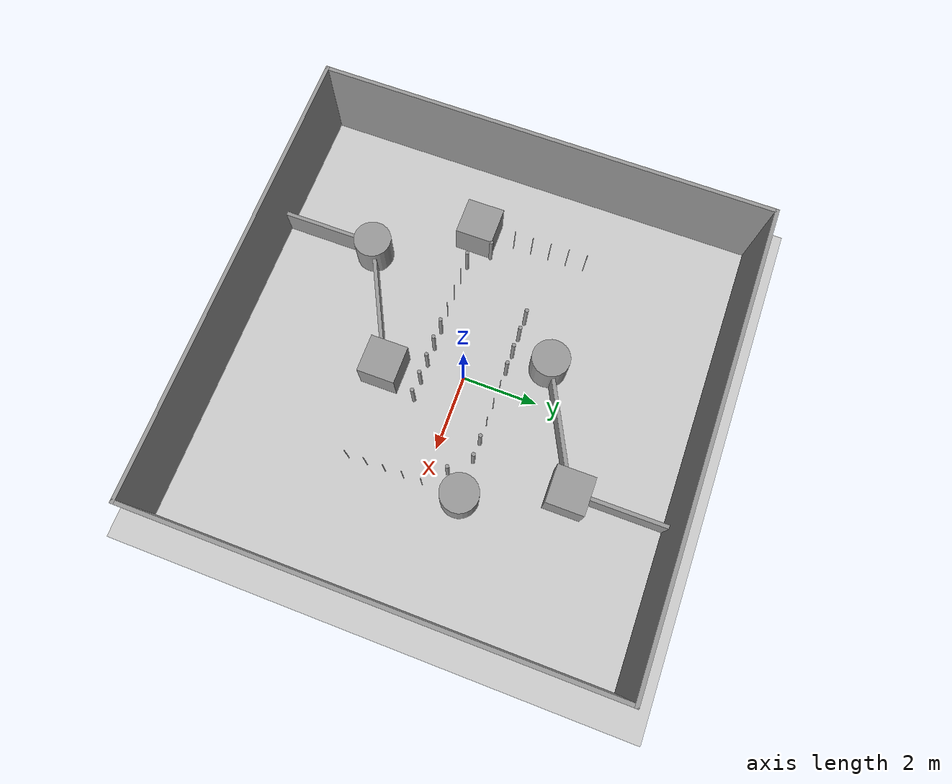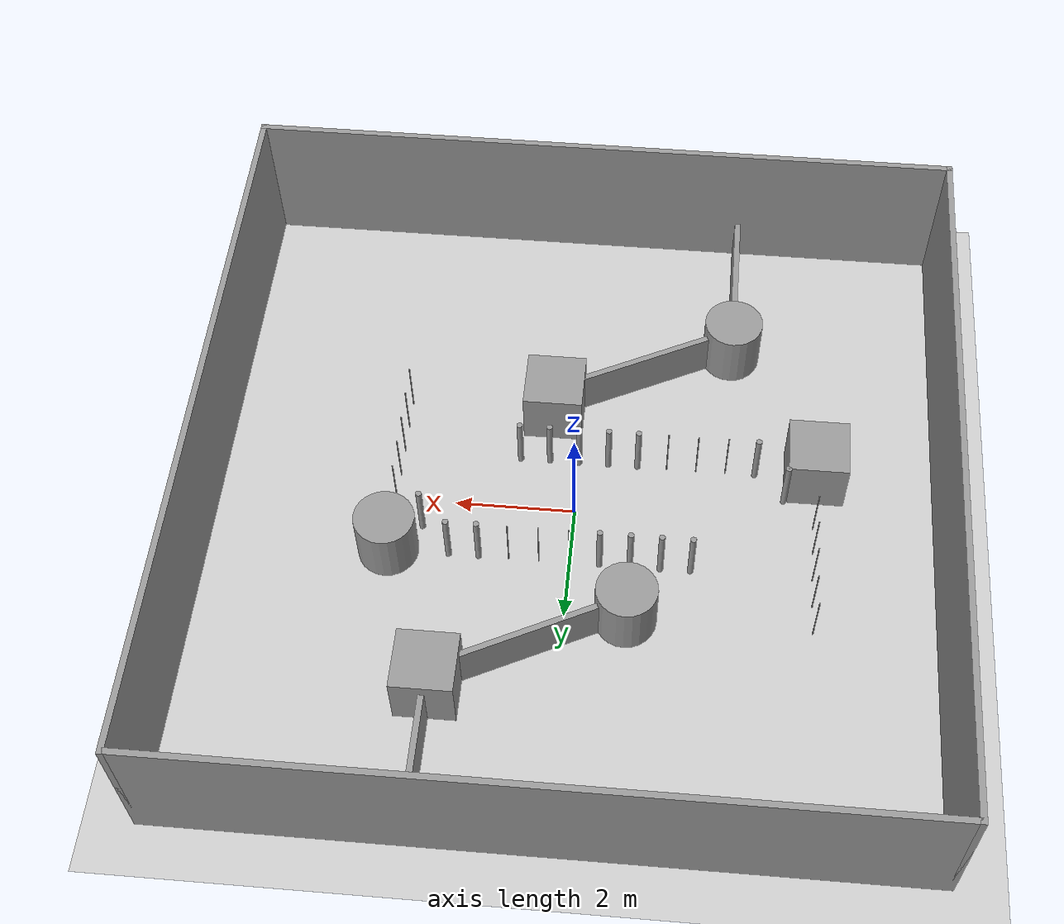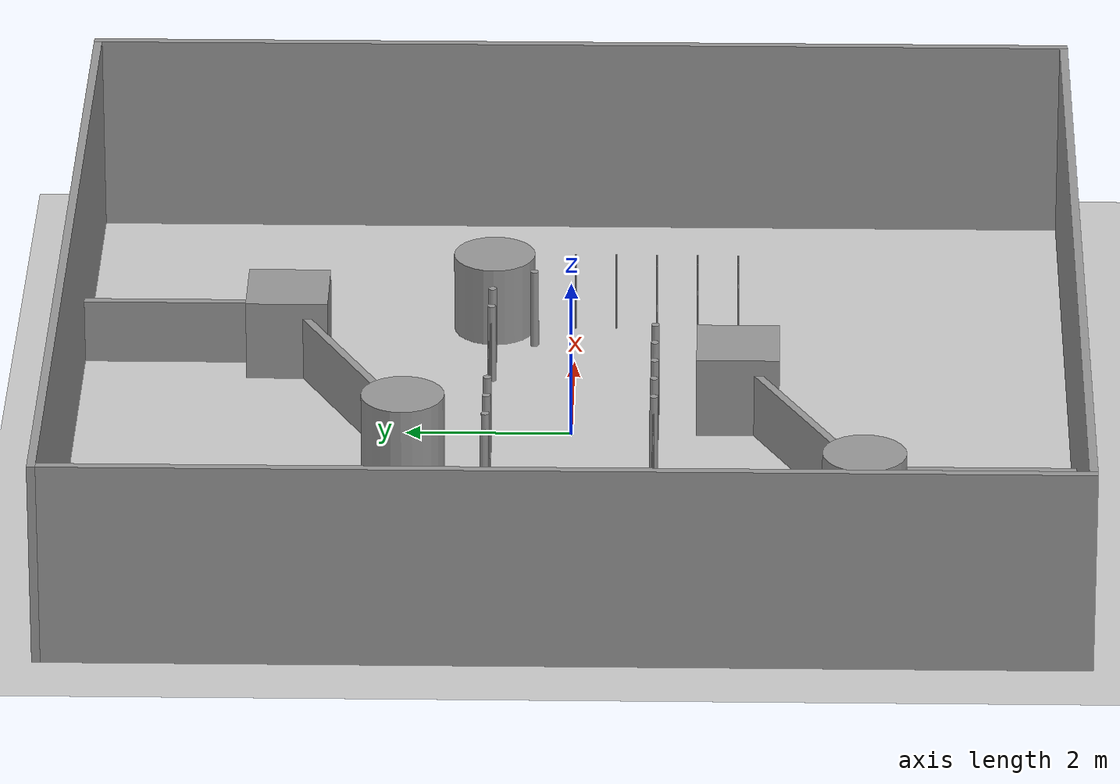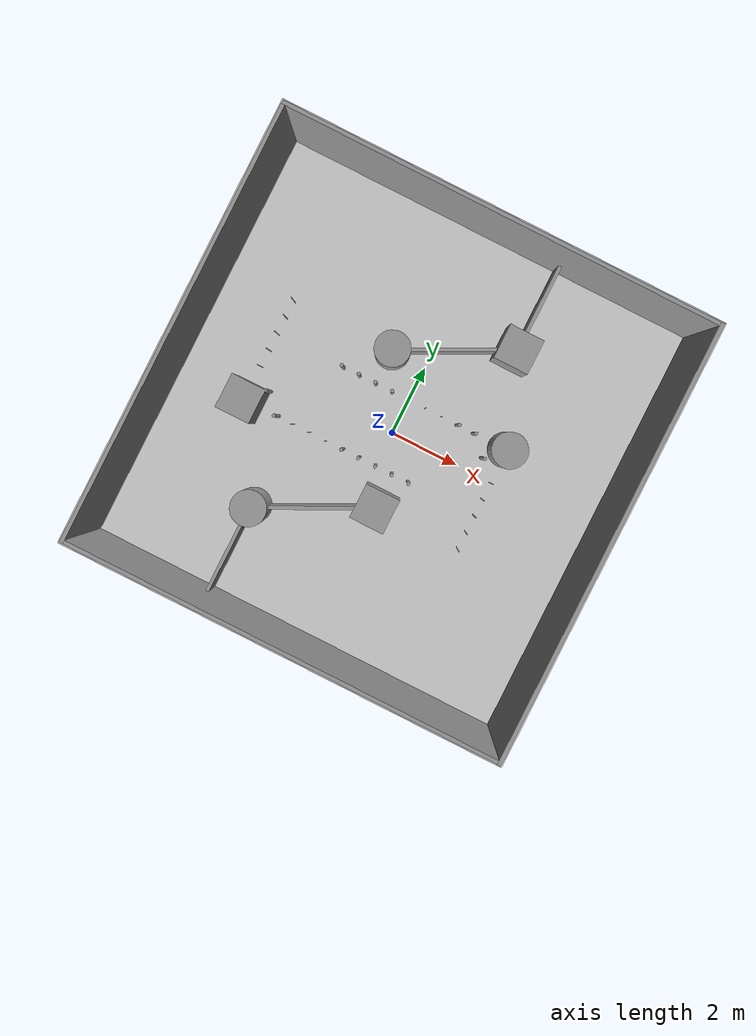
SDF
<sdf version="1.7">
 <world name="default">
  <light name="sun" type="directional">
   <pose>0 0 10 0 -0 0</pose>
   <diffuse>0.8 0.8 0.8 1</diffuse>
   <specular>0.2 0.2 0.2 1</specular>
   <attenuation>
    <range>1000</range>
    <constant>0.9</constant>
    <linear>0.01</linear>
    <quadratic>0.001</quadratic>
   </attenuation>
   <direction>-0.5 0.1 -0.9</direction>
   <spot><inner_angle>0</inner_angle><outer_angle>0</outer_angle><falloff>0</falloff></spot>
  </light>
  <model name="ground_plane">
   <static>1</static>
   <link name="link">
    <collision name="collision">
     <geometry><plane><normal>0 0 1</normal><size>100 100</size></plane></geometry>
     <surface>
      <contact><collide_bitmask>65535</collide_bitmask></contact>
      <friction><ode><mu>100</mu><mu2>50</mu2></ode></friction>
     </surface>
    </collision>
    <visual name="visual">
     <cast_shadows>0</cast_shadows>
     <geometry><plane><normal>0 0 1</normal><size>100 100</size></plane></geometry>
     <material>
      <script><uri>file://media/materials/scripts/gazebo.material</uri><name>Gazebo/Grey</name></script>
     </material>
    </visual>
   </link>
  </model>
  <gravity>0 0 -9.8</gravity>
  <magnetic_field>6e-06 2.3e-05 -4.2e-05</magnetic_field>
  <atmosphere type="adiabatic"/>
  <physics type="ode">
   <max_step_size>0.001</max_step_size>
   <real_time_factor>1</real_time_factor>
   <real_time_update_rate>1000</real_time_update_rate>
  </physics>
  <scene><ambient>0.4 0.4 0.4 1</ambient><background>0.7 0.7 0.7 1</background><shadows>1</shadows></scene>
  <spherical_coordinates>
   <surface_model>EARTH_WGS84</surface_model>
   <latitude_deg>0</latitude_deg>
   <longitude_deg>0</longitude_deg>
   <elevation>0</elevation>
   <heading_deg>0</heading_deg>
  </spherical_coordinates>
  <model name="wall_square">
   <link name="Wall_10">
    <collision name="Wall_10_Collision">
     <geometry><box><size>12.2 0.1 2.5</size></box></geometry>
     <pose>0 0 1.25 0 -0 0</pose>
    </collision>
    <visual name="Wall_10_Visual">
     <pose>0 0 1.25 0 -0 0</pose>
     <geometry><box><size>12.2 0.1 2.5</size></box></geometry>
     <material>
      <script><uri>file://media/materials/scripts/gazebo.material</uri><name>Gazebo/Grey</name></script>
      <ambient>1 1 1 1</ambient>
     </material>
     <meta><layer>0</layer></meta>
    </visual>
    <pose>6.05 0 0 0 -0 -1.5708</pose>
   </link>
   <link name="Wall_4">
    <collision name="Wall_4_Collision">
     <geometry><box><size>12.2 0.1 2.5</size></box></geometry>
     <pose>0 0 1.25 0 -0 0</pose>
    </collision>
    <visual name="Wall_4_Visual">
     <pose>0 0 1.25 0 -0 0</pose>
     <geometry><box><size>12.2 0.1 2.5</size></box></geometry>
     <material>
      <script><uri>file://media/materials/scripts/gazebo.material</uri><name>Gazebo/Grey</name></script>
      <ambient>1 1 1 1</ambient>
     </material>
     <meta><layer>0</layer></meta>
    </visual>
    <pose>0 6.05 0 0 -0 0</pose>
   </link>
   <link name="Wall_6">
    <collision name="Wall_6_Collision">
     <geometry><box><size>12.2 0.1 2.5</size></box></geometry>
     <pose>0 0 1.25 0 -0 0</pose>
    </collision>
    <visual name="Wall_6_Visual">
     <pose>0 0 1.25 0 -0 0</pose>
     <geometry><box><size>12.2 0.1 2.5</size></box></geometry>
     <material>
      <script><uri>file://media/materials/scripts/gazebo.material</uri><name>Gazebo/Grey</name></script>
      <ambient>1 1 1 1</ambient>
     </material>
     <meta><layer>0</layer></meta>
    </visual>
    <pose>-6.05 0 0 0 -0 -1.5708</pose>
   </link>
   <link name="Wall_8">
    <collision name="Wall_8_Collision">
     <geometry><box><size>12.2 0.1 2.5</size></box></geometry>
     <pose>0 0 1.25 0 -0 0</pose>
    </collision>
    <visual name="Wall_8_Visual">
     <pose>0 0 1.25 0 -0 0</pose>
     <geometry><box><size>12.2 0.1 2.5</size></box></geometry>
     <material>
      <script><uri>file://media/materials/scripts/gazebo.material</uri><name>Gazebo/Grey</name></script>
      <ambient>1 1 1 1</ambient>
     </material>
     <meta><layer>0</layer></meta>
    </visual>
    <pose>0 -6.05 0 0 -0 0</pose>
   </link>
   <static>1</static>
  </model>
  <model name="wall_connected">
   <pose>-1 -1.78354 0 0 -0 0</pose>
   <link name="Wall_12">
    <collision name="Wall_12_Collision">
     <geometry><box><size>3.4541 0.1 0.8</size></box></geometry>
     <pose>0 0 0.4 0 -0 0</pose>
    </collision>
    <visual name="Wall_12_Visual">
     <pose>0 0 0.4 0 -0 0</pose>
     <geometry><box><size>3.4541 0.1 0.8</size></box></geometry>
     <material>
      <script><uri>file://media/materials/scripts/gazebo.material</uri><name>Gazebo/Grey</name></script>
      <ambient>1 1 1 1</ambient>
     </material>
     <meta><layer>0</layer></meta>
    </visual>
    <pose>0 -0.966459 0 0 -0 -2.67794</pose>
   </link>
   <static>1</static>
  </model>
  <model name="wall_connected_1">
   <pose>0.5 1.78354 0 0 -0 0</pose>
   <link name="Wall_14">
    <collision name="Wall_14_Collision">
     <geometry><box><size>3.4541 0.1 0.8</size></box></geometry>
     <pose>0 0 0.4 0 -0 0</pose>
    </collision>
    <visual name="Wall_14_Visual">
     <pose>0 0 0.4 0 -0 0</pose>
     <geometry><box><size>3.4541 0.1 0.8</size></box></geometry>
     <material>
      <script><uri>file://media/materials/scripts/gazebo.material</uri><name>Gazebo/Grey</name></script>
      <ambient>1 1 1 1</ambient>
     </material>
     <meta><layer>0</layer></meta>
    </visual>
    <pose>0 0.966459 0 0 -0 0.463648</pose>
   </link>
   <static>1</static>
  </model>
  <model name="closing_wall">
   <pose>-0.25 0 0 0 -0 0</pose>
   <link name="Wall_18">
    <collision name="Wall_18_Collision">
     <geometry><box><size>2.6 0.1 0.8</size></box></geometry>
     <pose>0 0 0.4 0 -0 0</pose>
    </collision>
    <visual name="Wall_18_Visual">
     <pose>0 0 0.4 0 -0 0</pose>
     <geometry><box><size>2.6 0.1 0.8</size></box></geometry>
     <material>
      <script><uri>file://media/materials/scripts/gazebo.material</uri><name>Gazebo/Grey</name></script>
      <ambient>1 1 1 1</ambient>
     </material>
     <meta><layer>0</layer></meta>
    </visual>
    <pose>2.25 4.75 0 0 -0 1.5708</pose>
   </link>
   <link name="Wall_20">
    <collision name="Wall_20_Collision">
     <geometry><box><size>2.6 0.1 0.8</size></box></geometry>
     <pose>0 0 0.4 0 -0 0</pose>
    </collision>
    <visual name="Wall_20_Visual">
     <pose>0 0 0.4 0 -0 0</pose>
     <geometry><box><size>2.6 0.1 0.8</size></box></geometry>
     <material>
      <script><uri>file://media/materials/scripts/gazebo.material</uri><name>Gazebo/Grey</name></script>
      <ambient>1 1 1 1</ambient>
     </material>
     <meta><layer>0</layer></meta>
    </visual>
    <pose>-2.25 -4.75 0 0 -0 -1.5708</pose>
   </link>
   <static>1</static>
  </model>
  <model name="Cylindar_r01_static_clone_1">
   <link name="link_0">
    <inertial>
     <mass>1</mass>
     <inertia><ixx>0.145833</ixx><ixy>0</ixy><ixz>0</ixz><iyy>0.145833</iyy><iyz>0</iyz><izz>0.125</izz></inertia>
    </inertial>
    <visual name="visual">
     <geometry><cylinder><radius>0.05</radius><length>1</length></cylinder></geometry>
     <material>
      <lighting>1</lighting>
      <script><uri>file://media/materials/scripts/gazebo.material</uri><name>Gazebo/Grey</name></script>
      <shader type="pixel"><normal_map>__default__</normal_map></shader>
      <ambient>0.3 0.3 0.3 1</ambient>
      <diffuse>0.7 0.7 0.7 1</diffuse>
      <specular>0.01 0.01 0.01 1</specular>
      <emissive>0 0 0 1</emissive>
     </material>
    </visual>
    <collision name="collision">
     <geometry><cylinder><radius>0.05</radius><length>1</length></cylinder></geometry>
     <surface>
      <friction>
       <ode><mu>1</mu><mu2>1</mu2><fdir1>0 0 0</fdir1><slip1>0</slip1><slip2>0</slip2></ode>
       <torsional>
        <coefficient>1</coefficient>
        <patch_radius>0</patch_radius>
        <surface_radius>0</surface_radius>
        <use_patch_radius>1</use_patch_radius>
        <ode><slip>0</slip></ode>
       </torsional>
      </friction>
      <bounce><restitution_coefficient>0</restitution_coefficient><threshold>1e+06</threshold></bounce>
      <contact>
       <collide_without_contact>0</collide_without_contact>
       <collide_without_contact_bitmask>1</collide_without_contact_bitmask>
       <collide_bitmask>1</collide_bitmask>
       <ode>
        <soft_cfm>0</soft_cfm>
        <soft_erp>0.2</soft_erp>
        <kp>1e+13</kp>
        <kd>1</kd>
        <max_vel>0.01</max_vel>
        <min_depth>0</min_depth>
       </ode>
       <bullet>
        <split_impulse>1</split_impulse>
        <split_impulse_penetration_threshold>-0.01</split_impulse_penetration_threshold>
        <soft_cfm>0</soft_cfm>
        <soft_erp>0.2</soft_erp>
        <kp>1e+13</kp>
        <kd>1</kd>
       </bullet>
      </contact>
     </surface>
    </collision>
   </link>
   <static>1</static>
   <pose>1.5 1 0.5 0 -0 0</pose>
  </model>
  <model name="Cylindar_r01_static_clone_2">
   <link name="link_0">
    <inertial>
     <mass>1</mass>
     <inertia><ixx>0.145833</ixx><ixy>0</ixy><ixz>0</ixz><iyy>0.145833</iyy><iyz>0</iyz><izz>0.125</izz></inertia>
    </inertial>
    <visual name="visual">
     <geometry><cylinder><radius>0.05</radius><length>1</length></cylinder></geometry>
     <material>
      <lighting>1</lighting>
      <script><uri>file://media/materials/scripts/gazebo.material</uri><name>Gazebo/Grey</name></script>
      <shader type="pixel"><normal_map>__default__</normal_map></shader>
      <ambient>0.3 0.3 0.3 1</ambient>
      <diffuse>0.7 0.7 0.7 1</diffuse>
      <specular>0.01 0.01 0.01 1</specular>
      <emissive>0 0 0 1</emissive>
     </material>
    </visual>
    <collision name="collision">
     <geometry><cylinder><radius>0.05</radius><length>1</length></cylinder></geometry>
     <surface>
      <friction>
       <ode><mu>1</mu><mu2>1</mu2><fdir1>0 0 0</fdir1><slip1>0</slip1><slip2>0</slip2></ode>
       <torsional>
        <coefficient>1</coefficient>
        <patch_radius>0</patch_radius>
        <surface_radius>0</surface_radius>
        <use_patch_radius>1</use_patch_radius>
        <ode><slip>0</slip></ode>
       </torsional>
      </friction>
      <bounce><restitution_coefficient>0</restitution_coefficient><threshold>1e+06</threshold></bounce>
      <contact>
       <collide_without_contact>0</collide_without_contact>
       <collide_without_contact_bitmask>1</collide_without_contact_bitmask>
       <collide_bitmask>1</collide_bitmask>
       <ode>
        <soft_cfm>0</soft_cfm>
        <soft_erp>0.2</soft_erp>
        <kp>1e+13</kp>
        <kd>1</kd>
        <max_vel>0.01</max_vel>
        <min_depth>0</min_depth>
       </ode>
       <bullet>
        <split_impulse>1</split_impulse>
        <split_impulse_penetration_threshold>-0.01</split_impulse_penetration_threshold>
        <soft_cfm>0</soft_cfm>
        <soft_erp>0.2</soft_erp>
        <kp>1e+13</kp>
        <kd>1</kd>
       </bullet>
      </contact>
     </surface>
    </collision>
   </link>
   <static>1</static>
   <pose>2 1 0.5 0 -0 0</pose>
  </model>
  <model name="Cylindar_r01_static_clone_3">
   <link name="link_0">
    <inertial>
     <mass>1</mass>
     <inertia><ixx>0.145833</ixx><ixy>0</ixy><ixz>0</ixz><iyy>0.145833</iyy><iyz>0</iyz><izz>0.125</izz></inertia>
    </inertial>
    <visual name="visual">
     <geometry><cylinder><radius>0.05</radius><length>1</length></cylinder></geometry>
     <material>
      <lighting>1</lighting>
      <script><uri>file://media/materials/scripts/gazebo.material</uri><name>Gazebo/Grey</name></script>
      <shader type="pixel"><normal_map>__default__</normal_map></shader>
      <ambient>0.3 0.3 0.3 1</ambient>
      <diffuse>0.7 0.7 0.7 1</diffuse>
      <specular>0.01 0.01 0.01 1</specular>
      <emissive>0 0 0 1</emissive>
     </material>
    </visual>
    <collision name="collision">
     <geometry><cylinder><radius>0.05</radius><length>1</length></cylinder></geometry>
     <surface>
      <friction>
       <ode><mu>1</mu><mu2>1</mu2><fdir1>0 0 0</fdir1><slip1>0</slip1><slip2>0</slip2></ode>
       <torsional>
        <coefficient>1</coefficient>
        <patch_radius>0</patch_radius>
        <surface_radius>0</surface_radius>
        <use_patch_radius>1</use_patch_radius>
        <ode><slip>0</slip></ode>
       </torsional>
      </friction>
      <bounce><restitution_coefficient>0</restitution_coefficient><threshold>1e+06</threshold></bounce>
      <contact>
       <collide_without_contact>0</collide_without_contact>
       <collide_without_contact_bitmask>1</collide_without_contact_bitmask>
       <collide_bitmask>1</collide_bitmask>
       <ode>
        <soft_cfm>0</soft_cfm>
        <soft_erp>0.2</soft_erp>
        <kp>1e+13</kp>
        <kd>1</kd>
        <max_vel>0.01</max_vel>
        <min_depth>0</min_depth>
       </ode>
       <bullet>
        <split_impulse>1</split_impulse>
        <split_impulse_penetration_threshold>-0.01</split_impulse_penetration_threshold>
        <soft_cfm>0</soft_cfm>
        <soft_erp>0.2</soft_erp>
        <kp>1e+13</kp>
        <kd>1</kd>
       </bullet>
      </contact>
     </surface>
    </collision>
   </link>
   <static>1</static>
   <pose>-0.5 1 0.5 0 -0 0</pose>
  </model>
  <model name="Cylindar_r01_static_clone_4">
   <link name="link_0">
    <inertial>
     <mass>1</mass>
     <inertia><ixx>0.145833</ixx><ixy>0</ixy><ixz>0</ixz><iyy>0.145833</iyy><iyz>0</iyz><izz>0.125</izz></inertia>
    </inertial>
    <visual name="visual">
     <geometry><cylinder><radius>0.05</radius><length>1</length></cylinder></geometry>
     <material>
      <lighting>1</lighting>
      <script><uri>file://media/materials/scripts/gazebo.material</uri><name>Gazebo/Grey</name></script>
      <shader type="pixel"><normal_map>__default__</normal_map></shader>
      <ambient>0.3 0.3 0.3 1</ambient>
      <diffuse>0.7 0.7 0.7 1</diffuse>
      <specular>0.01 0.01 0.01 1</specular>
      <emissive>0 0 0 1</emissive>
     </material>
    </visual>
    <collision name="collision">
     <geometry><cylinder><radius>0.05</radius><length>1</length></cylinder></geometry>
     <surface>
      <friction>
       <ode><mu>1</mu><mu2>1</mu2><fdir1>0 0 0</fdir1><slip1>0</slip1><slip2>0</slip2></ode>
       <torsional>
        <coefficient>1</coefficient>
        <patch_radius>0</patch_radius>
        <surface_radius>0</surface_radius>
        <use_patch_radius>1</use_patch_radius>
        <ode><slip>0</slip></ode>
       </torsional>
      </friction>
      <bounce><restitution_coefficient>0</restitution_coefficient><threshold>1e+06</threshold></bounce>
      <contact>
       <collide_without_contact>0</collide_without_contact>
       <collide_without_contact_bitmask>1</collide_without_contact_bitmask>
       <collide_bitmask>1</collide_bitmask>
       <ode>
        <soft_cfm>0</soft_cfm>
        <soft_erp>0.2</soft_erp>
        <kp>1e+13</kp>
        <kd>1</kd>
        <max_vel>0.01</max_vel>
        <min_depth>0</min_depth>
       </ode>
       <bullet>
        <split_impulse>1</split_impulse>
        <split_impulse_penetration_threshold>-0.01</split_impulse_penetration_threshold>
        <soft_cfm>0</soft_cfm>
        <soft_erp>0.2</soft_erp>
        <kp>1e+13</kp>
        <kd>1</kd>
       </bullet>
      </contact>
     </surface>
    </collision>
   </link>
   <static>1</static>
   <pose>-1 1 0.5 0 -0 0</pose>
  </model>
  <model name="Cylindar_r01_static_clone_5">
   <link name="link_0">
    <inertial>
     <mass>1</mass>
     <inertia><ixx>0.145833</ixx><ixy>0</ixy><ixz>0</ixz><iyy>0.145833</iyy><iyz>0</iyz><izz>0.125</izz></inertia>
    </inertial>
    <visual name="visual">
     <geometry><cylinder><radius>0.05</radius><length>1</length></cylinder></geometry>
     <material>
      <lighting>1</lighting>
      <script><uri>file://media/materials/scripts/gazebo.material</uri><name>Gazebo/Grey</name></script>
      <shader type="pixel"><normal_map>__default__</normal_map></shader>
      <ambient>0.3 0.3 0.3 1</ambient>
      <diffuse>0.7 0.7 0.7 1</diffuse>
      <specular>0.01 0.01 0.01 1</specular>
      <emissive>0 0 0 1</emissive>
     </material>
    </visual>
    <collision name="collision">
     <geometry><cylinder><radius>0.05</radius><length>1</length></cylinder></geometry>
     <surface>
      <friction>
       <ode><mu>1</mu><mu2>1</mu2><fdir1>0 0 0</fdir1><slip1>0</slip1><slip2>0</slip2></ode>
       <torsional>
        <coefficient>1</coefficient>
        <patch_radius>0</patch_radius>
        <surface_radius>0</surface_radius>
        <use_patch_radius>1</use_patch_radius>
        <ode><slip>0</slip></ode>
       </torsional>
      </friction>
      <bounce><restitution_coefficient>0</restitution_coefficient><threshold>1e+06</threshold></bounce>
      <contact>
       <collide_without_contact>0</collide_without_contact>
       <collide_without_contact_bitmask>1</collide_without_contact_bitmask>
       <collide_bitmask>1</collide_bitmask>
       <ode>
        <soft_cfm>0</soft_cfm>
        <soft_erp>0.2</soft_erp>
        <kp>1e+13</kp>
        <kd>1</kd>
        <max_vel>0.01</max_vel>
        <min_depth>0</min_depth>
       </ode>
       <bullet>
        <split_impulse>1</split_impulse>
        <split_impulse_penetration_threshold>-0.01</split_impulse_penetration_threshold>
        <soft_cfm>0</soft_cfm>
        <soft_erp>0.2</soft_erp>
        <kp>1e+13</kp>
        <kd>1</kd>
       </bullet>
      </contact>
     </surface>
    </collision>
   </link>
   <static>1</static>
   <pose>-1.5 1 0.5 0 -0 0</pose>
  </model>
  <model name="Cylindar_r01_static_clone_6">
   <link name="link_0">
    <inertial>
     <mass>1</mass>
     <inertia><ixx>0.145833</ixx><ixy>0</ixy><ixz>0</ixz><iyy>0.145833</iyy><iyz>0</iyz><izz>0.125</izz></inertia>
    </inertial>
    <visual name="visual">
     <geometry><cylinder><radius>0.05</radius><length>1</length></cylinder></geometry>
     <material>
      <lighting>1</lighting>
      <script><uri>file://media/materials/scripts/gazebo.material</uri><name>Gazebo/Grey</name></script>
      <shader type="pixel"><normal_map>__default__</normal_map></shader>
      <ambient>0.3 0.3 0.3 1</ambient>
      <diffuse>0.7 0.7 0.7 1</diffuse>
      <specular>0.01 0.01 0.01 1</specular>
      <emissive>0 0 0 1</emissive>
     </material>
    </visual>
    <collision name="collision">
     <geometry><cylinder><radius>0.05</radius><length>1</length></cylinder></geometry>
     <surface>
      <friction>
       <ode><mu>1</mu><mu2>1</mu2><fdir1>0 0 0</fdir1><slip1>0</slip1><slip2>0</slip2></ode>
       <torsional>
        <coefficient>1</coefficient>
        <patch_radius>0</patch_radius>
        <surface_radius>0</surface_radius>
        <use_patch_radius>1</use_patch_radius>
        <ode><slip>0</slip></ode>
       </torsional>
      </friction>
      <bounce><restitution_coefficient>0</restitution_coefficient><threshold>1e+06</threshold></bounce>
      <contact>
       <collide_without_contact>0</collide_without_contact>
       <collide_without_contact_bitmask>1</collide_without_contact_bitmask>
       <collide_bitmask>1</collide_bitmask>
       <ode>
        <soft_cfm>0</soft_cfm>
        <soft_erp>0.2</soft_erp>
        <kp>1e+13</kp>
        <kd>1</kd>
        <max_vel>0.01</max_vel>
        <min_depth>0</min_depth>
       </ode>
       <bullet>
        <split_impulse>1</split_impulse>
        <split_impulse_penetration_threshold>-0.01</split_impulse_penetration_threshold>
        <soft_cfm>0</soft_cfm>
        <soft_erp>0.2</soft_erp>
        <kp>1e+13</kp>
        <kd>1</kd>
       </bullet>
      </contact>
     </surface>
    </collision>
   </link>
   <static>1</static>
   <pose>-2 1 0.5 0 -0 0</pose>
  </model>
  <model name="Cylindar_r01_static_clone_6_clone">
   <link name="link_0">
    <inertial>
     <mass>1</mass>
     <inertia><ixx>0.145833</ixx><ixy>0</ixy><ixz>0</ixz><iyy>0.145833</iyy><iyz>0</iyz><izz>0.125</izz></inertia>
    </inertial>
    <visual name="visual">
     <geometry><cylinder><radius>0.05</radius><length>1</length></cylinder></geometry>
     <material>
      <lighting>1</lighting>
      <script><uri>file://media/materials/scripts/gazebo.material</uri><name>Gazebo/Grey</name></script>
      <shader type="pixel"><normal_map>__default__</normal_map></shader>
      <ambient>0.3 0.3 0.3 1</ambient>
      <diffuse>0.7 0.7 0.7 1</diffuse>
      <specular>0.01 0.01 0.01 1</specular>
      <emissive>0 0 0 1</emissive>
     </material>
    </visual>
    <collision name="collision">
     <geometry><cylinder><radius>0.05</radius><length>1</length></cylinder></geometry>
     <surface>
      <friction>
       <ode><mu>1</mu><mu2>1</mu2><fdir1>0 0 0</fdir1><slip1>0</slip1><slip2>0</slip2></ode>
       <torsional>
        <coefficient>1</coefficient>
        <patch_radius>0</patch_radius>
        <surface_radius>0</surface_radius>
        <use_patch_radius>1</use_patch_radius>
        <ode><slip>0</slip></ode>
       </torsional>
      </friction>
      <bounce><restitution_coefficient>0</restitution_coefficient><threshold>1e+06</threshold></bounce>
      <contact>
       <collide_without_contact>0</collide_without_contact>
       <collide_without_contact_bitmask>1</collide_without_contact_bitmask>
       <collide_bitmask>1</collide_bitmask>
       <ode>
        <soft_cfm>0</soft_cfm>
        <soft_erp>0.2</soft_erp>
        <kp>1e+13</kp>
        <kd>1</kd>
        <max_vel>0.01</max_vel>
        <min_depth>0</min_depth>
       </ode>
       <bullet>
        <split_impulse>1</split_impulse>
        <split_impulse_penetration_threshold>-0.01</split_impulse_penetration_threshold>
        <soft_cfm>0</soft_cfm>
        <soft_erp>0.2</soft_erp>
        <kp>1e+13</kp>
        <kd>1</kd>
       </bullet>
      </contact>
     </surface>
    </collision>
   </link>
   <static>1</static>
   <pose>-3 -1 0.5 0 -0 0</pose>
  </model>
  <model name="Cylindar_r01_static_clone_6_clone_3">
   <link name="link_0">
    <inertial>
     <mass>1</mass>
     <inertia><ixx>0.145833</ixx><ixy>0</ixy><ixz>0</ixz><iyy>0.145833</iyy><iyz>0</iyz><izz>0.125</izz></inertia>
    </inertial>
    <visual name="visual">
     <geometry><cylinder><radius>0.05</radius><length>1</length></cylinder></geometry>
     <material>
      <lighting>1</lighting>
      <script><uri>file://media/materials/scripts/gazebo.material</uri><name>Gazebo/Grey</name></script>
      <shader type="pixel"><normal_map>__default__</normal_map></shader>
      <ambient>0.3 0.3 0.3 1</ambient>
      <diffuse>0.7 0.7 0.7 1</diffuse>
      <specular>0.01 0.01 0.01 1</specular>
      <emissive>0 0 0 1</emissive>
     </material>
    </visual>
    <collision name="collision">
     <geometry><cylinder><radius>0.05</radius><length>1</length></cylinder></geometry>
     <surface>
      <friction>
       <ode><mu>1</mu><mu2>1</mu2><fdir1>0 0 0</fdir1><slip1>0</slip1><slip2>0</slip2></ode>
       <torsional>
        <coefficient>1</coefficient>
        <patch_radius>0</patch_radius>
        <surface_radius>0</surface_radius>
        <use_patch_radius>1</use_patch_radius>
        <ode><slip>0</slip></ode>
       </torsional>
      </friction>
      <bounce><restitution_coefficient>0</restitution_coefficient><threshold>1e+06</threshold></bounce>
      <contact>
       <collide_without_contact>0</collide_without_contact>
       <collide_without_contact_bitmask>1</collide_without_contact_bitmask>
       <collide_bitmask>1</collide_bitmask>
       <ode>
        <soft_cfm>0</soft_cfm>
        <soft_erp>0.2</soft_erp>
        <kp>1e+13</kp>
        <kd>1</kd>
        <max_vel>0.01</max_vel>
        <min_depth>0</min_depth>
       </ode>
       <bullet>
        <split_impulse>1</split_impulse>
        <split_impulse_penetration_threshold>-0.01</split_impulse_penetration_threshold>
        <soft_cfm>0</soft_cfm>
        <soft_erp>0.2</soft_erp>
        <kp>1e+13</kp>
        <kd>1</kd>
       </bullet>
      </contact>
     </surface>
    </collision>
   </link>
   <static>1</static>
   <pose>-1 -1 0.5 0 -0 0</pose>
  </model>
  <model name="Cylindar_r01_static_clone_6_clone_4">
   <link name="link_0">
    <inertial>
     <mass>1</mass>
     <inertia><ixx>0.145833</ixx><ixy>0</ixy><ixz>0</ixz><iyy>0.145833</iyy><iyz>0</iyz><izz>0.125</izz></inertia>
    </inertial>
    <visual name="visual">
     <geometry><cylinder><radius>0.05</radius><length>1</length></cylinder></geometry>
     <material>
      <lighting>1</lighting>
      <script><uri>file://media/materials/scripts/gazebo.material</uri><name>Gazebo/Grey</name></script>
      <shader type="pixel"><normal_map>__default__</normal_map></shader>
      <ambient>0.3 0.3 0.3 1</ambient>
      <diffuse>0.7 0.7 0.7 1</diffuse>
      <specular>0.01 0.01 0.01 1</specular>
      <emissive>0 0 0 1</emissive>
     </material>
    </visual>
    <collision name="collision">
     <geometry><cylinder><radius>0.05</radius><length>1</length></cylinder></geometry>
     <surface>
      <friction>
       <ode><mu>1</mu><mu2>1</mu2><fdir1>0 0 0</fdir1><slip1>0</slip1><slip2>0</slip2></ode>
       <torsional>
        <coefficient>1</coefficient>
        <patch_radius>0</patch_radius>
        <surface_radius>0</surface_radius>
        <use_patch_radius>1</use_patch_radius>
        <ode><slip>0</slip></ode>
       </torsional>
      </friction>
      <bounce><restitution_coefficient>0</restitution_coefficient><threshold>1e+06</threshold></bounce>
      <contact>
       <collide_without_contact>0</collide_without_contact>
       <collide_without_contact_bitmask>1</collide_without_contact_bitmask>
       <collide_bitmask>1</collide_bitmask>
       <ode>
        <soft_cfm>0</soft_cfm>
        <soft_erp>0.2</soft_erp>
        <kp>1e+13</kp>
        <kd>1</kd>
        <max_vel>0.01</max_vel>
        <min_depth>0</min_depth>
       </ode>
       <bullet>
        <split_impulse>1</split_impulse>
        <split_impulse_penetration_threshold>-0.01</split_impulse_penetration_threshold>
        <soft_cfm>0</soft_cfm>
        <soft_erp>0.2</soft_erp>
        <kp>1e+13</kp>
        <kd>1</kd>
       </bullet>
      </contact>
     </surface>
    </collision>
   </link>
   <static>1</static>
   <pose>-0.5 -1 0.5 0 -0 0</pose>
  </model>
  <model name="Cylindar_r01_static_clone_6_clone_5">
   <link name="link_0">
    <inertial>
     <mass>1</mass>
     <inertia><ixx>0.145833</ixx><ixy>0</ixy><ixz>0</ixz><iyy>0.145833</iyy><iyz>0</iyz><izz>0.125</izz></inertia>
    </inertial>
    <visual name="visual">
     <geometry><cylinder><radius>0.05</radius><length>1</length></cylinder></geometry>
     <material>
      <lighting>1</lighting>
      <script><uri>file://media/materials/scripts/gazebo.material</uri><name>Gazebo/Grey</name></script>
      <shader type="pixel"><normal_map>__default__</normal_map></shader>
      <ambient>0.3 0.3 0.3 1</ambient>
      <diffuse>0.7 0.7 0.7 1</diffuse>
      <specular>0.01 0.01 0.01 1</specular>
      <emissive>0 0 0 1</emissive>
     </material>
    </visual>
    <collision name="collision">
     <geometry><cylinder><radius>0.05</radius><length>1</length></cylinder></geometry>
     <surface>
      <friction>
       <ode><mu>1</mu><mu2>1</mu2><fdir1>0 0 0</fdir1><slip1>0</slip1><slip2>0</slip2></ode>
       <torsional>
        <coefficient>1</coefficient>
        <patch_radius>0</patch_radius>
        <surface_radius>0</surface_radius>
        <use_patch_radius>1</use_patch_radius>
        <ode><slip>0</slip></ode>
       </torsional>
      </friction>
      <bounce><restitution_coefficient>0</restitution_coefficient><threshold>1e+06</threshold></bounce>
      <contact>
       <collide_without_contact>0</collide_without_contact>
       <collide_without_contact_bitmask>1</collide_without_contact_bitmask>
       <collide_bitmask>1</collide_bitmask>
       <ode>
        <soft_cfm>0</soft_cfm>
        <soft_erp>0.2</soft_erp>
        <kp>1e+13</kp>
        <kd>1</kd>
        <max_vel>0.01</max_vel>
        <min_depth>0</min_depth>
       </ode>
       <bullet>
        <split_impulse>1</split_impulse>
        <split_impulse_penetration_threshold>-0.01</split_impulse_penetration_threshold>
        <soft_cfm>0</soft_cfm>
        <soft_erp>0.2</soft_erp>
        <kp>1e+13</kp>
        <kd>1</kd>
       </bullet>
      </contact>
     </surface>
    </collision>
   </link>
   <static>1</static>
   <pose>0 -1 0.5 0 -0 0</pose>
  </model>
  <model name="Cylindar_r01_static_clone_6_clone_6">
   <link name="link_0">
    <inertial>
     <mass>1</mass>
     <inertia><ixx>0.145833</ixx><ixy>0</ixy><ixz>0</ixz><iyy>0.145833</iyy><iyz>0</iyz><izz>0.125</izz></inertia>
    </inertial>
    <visual name="visual">
     <geometry><cylinder><radius>0.05</radius><length>1</length></cylinder></geometry>
     <material>
      <lighting>1</lighting>
      <script><uri>file://media/materials/scripts/gazebo.material</uri><name>Gazebo/Grey</name></script>
      <shader type="pixel"><normal_map>__default__</normal_map></shader>
      <ambient>0.3 0.3 0.3 1</ambient>
      <diffuse>0.7 0.7 0.7 1</diffuse>
      <specular>0.01 0.01 0.01 1</specular>
      <emissive>0 0 0 1</emissive>
     </material>
    </visual>
    <collision name="collision">
     <geometry><cylinder><radius>0.05</radius><length>1</length></cylinder></geometry>
     <surface>
      <friction>
       <ode><mu>1</mu><mu2>1</mu2><fdir1>0 0 0</fdir1><slip1>0</slip1><slip2>0</slip2></ode>
       <torsional>
        <coefficient>1</coefficient>
        <patch_radius>0</patch_radius>
        <surface_radius>0</surface_radius>
        <use_patch_radius>1</use_patch_radius>
        <ode><slip>0</slip></ode>
       </torsional>
      </friction>
      <bounce><restitution_coefficient>0</restitution_coefficient><threshold>1e+06</threshold></bounce>
      <contact>
       <collide_without_contact>0</collide_without_contact>
       <collide_without_contact_bitmask>1</collide_without_contact_bitmask>
       <collide_bitmask>1</collide_bitmask>
       <ode>
        <soft_cfm>0</soft_cfm>
        <soft_erp>0.2</soft_erp>
        <kp>1e+13</kp>
        <kd>1</kd>
        <max_vel>0.01</max_vel>
        <min_depth>0</min_depth>
       </ode>
       <bullet>
        <split_impulse>1</split_impulse>
        <split_impulse_penetration_threshold>-0.01</split_impulse_penetration_threshold>
        <soft_cfm>0</soft_cfm>
        <soft_erp>0.2</soft_erp>
        <kp>1e+13</kp>
        <kd>1</kd>
       </bullet>
      </contact>
     </surface>
    </collision>
   </link>
   <static>1</static>
   <pose>0.5 -1 0.5 0 -0 0</pose>
  </model>
  <model name="Cylindar_r01_static_clone_6_clone_7">
   <link name="link_0">
    <inertial>
     <mass>1</mass>
     <inertia><ixx>0.145833</ixx><ixy>0</ixy><ixz>0</ixz><iyy>0.145833</iyy><iyz>0</iyz><izz>0.125</izz></inertia>
    </inertial>
    <visual name="visual">
     <geometry><cylinder><radius>0.05</radius><length>1</length></cylinder></geometry>
     <material>
      <lighting>1</lighting>
      <script><uri>file://media/materials/scripts/gazebo.material</uri><name>Gazebo/Grey</name></script>
      <shader type="pixel"><normal_map>__default__</normal_map></shader>
      <ambient>0.3 0.3 0.3 1</ambient>
      <diffuse>0.7 0.7 0.7 1</diffuse>
      <specular>0.01 0.01 0.01 1</specular>
      <emissive>0 0 0 1</emissive>
     </material>
    </visual>
    <collision name="collision">
     <geometry><cylinder><radius>0.05</radius><length>1</length></cylinder></geometry>
     <surface>
      <friction>
       <ode><mu>1</mu><mu2>1</mu2><fdir1>0 0 0</fdir1><slip1>0</slip1><slip2>0</slip2></ode>
       <torsional>
        <coefficient>1</coefficient>
        <patch_radius>0</patch_radius>
        <surface_radius>0</surface_radius>
        <use_patch_radius>1</use_patch_radius>
        <ode><slip>0</slip></ode>
       </torsional>
      </friction>
      <bounce><restitution_coefficient>0</restitution_coefficient><threshold>1e+06</threshold></bounce>
      <contact>
       <collide_without_contact>0</collide_without_contact>
       <collide_without_contact_bitmask>1</collide_without_contact_bitmask>
       <collide_bitmask>1</collide_bitmask>
       <ode>
        <soft_cfm>0</soft_cfm>
        <soft_erp>0.2</soft_erp>
        <kp>1e+13</kp>
        <kd>1</kd>
        <max_vel>0.01</max_vel>
        <min_depth>0</min_depth>
       </ode>
       <bullet>
        <split_impulse>1</split_impulse>
        <split_impulse_penetration_threshold>-0.01</split_impulse_penetration_threshold>
        <soft_cfm>0</soft_cfm>
        <soft_erp>0.2</soft_erp>
        <kp>1e+13</kp>
        <kd>1</kd>
       </bullet>
      </contact>
     </surface>
    </collision>
   </link>
   <static>1</static>
   <pose>1 -1 0.5 0 -0 0</pose>
  </model>
  <model name="Cylindar_r01_static_clone_2_clone">
   <link name="link_0">
    <inertial>
     <mass>1</mass>
     <inertia><ixx>0.145833</ixx><ixy>0</ixy><ixz>0</ixz><iyy>0.145833</iyy><iyz>0</iyz><izz>0.125</izz></inertia>
    </inertial>
    <visual name="visual">
     <geometry><cylinder><radius>0.05</radius><length>1</length></cylinder></geometry>
     <material>
      <lighting>1</lighting>
      <script><uri>file://media/materials/scripts/gazebo.material</uri><name>Gazebo/Grey</name></script>
      <shader type="pixel"><normal_map>__default__</normal_map></shader>
      <ambient>0.3 0.3 0.3 1</ambient>
      <diffuse>0.7 0.7 0.7 1</diffuse>
      <specular>0.01 0.01 0.01 1</specular>
      <emissive>0 0 0 1</emissive>
     </material>
    </visual>
    <collision name="collision">
     <geometry><cylinder><radius>0.05</radius><length>1</length></cylinder></geometry>
     <surface>
      <friction>
       <ode><mu>1</mu><mu2>1</mu2><fdir1>0 0 0</fdir1><slip1>0</slip1><slip2>0</slip2></ode>
       <torsional>
        <coefficient>1</coefficient>
        <patch_radius>0</patch_radius>
        <surface_radius>0</surface_radius>
        <use_patch_radius>1</use_patch_radius>
        <ode><slip>0</slip></ode>
       </torsional>
      </friction>
      <bounce><restitution_coefficient>0</restitution_coefficient><threshold>1e+06</threshold></bounce>
      <contact>
       <collide_without_contact>0</collide_without_contact>
       <collide_without_contact_bitmask>1</collide_without_contact_bitmask>
       <collide_bitmask>1</collide_bitmask>
       <ode>
        <soft_cfm>0</soft_cfm>
        <soft_erp>0.2</soft_erp>
        <kp>1e+13</kp>
        <kd>1</kd>
        <max_vel>0.01</max_vel>
        <min_depth>0</min_depth>
       </ode>
       <bullet>
        <split_impulse>1</split_impulse>
        <split_impulse_penetration_threshold>-0.01</split_impulse_penetration_threshold>
        <soft_cfm>0</soft_cfm>
        <soft_erp>0.2</soft_erp>
        <kp>1e+13</kp>
        <kd>1</kd>
       </bullet>
      </contact>
     </surface>
    </collision>
   </link>
   <static>1</static>
   <pose>2.5 0.5 0.5 0 -0 0</pose>
  </model>
  <model name="Cylindar_r01_static_clone_6_clone_clone">
   <link name="link_0">
    <inertial>
     <mass>1</mass>
     <inertia><ixx>0.145833</ixx><ixy>0</ixy><ixz>0</ixz><iyy>0.145833</iyy><iyz>0</iyz><izz>0.125</izz></inertia>
    </inertial>
    <visual name="visual">
     <geometry><cylinder><radius>0.05</radius><length>1</length></cylinder></geometry>
     <material>
      <lighting>1</lighting>
      <script><uri>file://media/materials/scripts/gazebo.material</uri><name>Gazebo/Grey</name></script>
      <shader type="pixel"><normal_map>__default__</normal_map></shader>
      <ambient>0.3 0.3 0.3 1</ambient>
      <diffuse>0.7 0.7 0.7 1</diffuse>
      <specular>0.01 0.01 0.01 1</specular>
      <emissive>0 0 0 1</emissive>
     </material>
    </visual>
    <collision name="collision">
     <geometry><cylinder><radius>0.05</radius><length>1</length></cylinder></geometry>
     <surface>
      <friction>
       <ode><mu>1</mu><mu2>1</mu2><fdir1>0 0 0</fdir1><slip1>0</slip1><slip2>0</slip2></ode>
       <torsional>
        <coefficient>1</coefficient>
        <patch_radius>0</patch_radius>
        <surface_radius>0</surface_radius>
        <use_patch_radius>1</use_patch_radius>
        <ode><slip>0</slip></ode>
       </torsional>
      </friction>
      <bounce><restitution_coefficient>0</restitution_coefficient><threshold>1e+06</threshold></bounce>
      <contact>
       <collide_without_contact>0</collide_without_contact>
       <collide_without_contact_bitmask>1</collide_without_contact_bitmask>
       <collide_bitmask>1</collide_bitmask>
       <ode>
        <soft_cfm>0</soft_cfm>
        <soft_erp>0.2</soft_erp>
        <kp>1e+13</kp>
        <kd>1</kd>
        <max_vel>0.01</max_vel>
        <min_depth>0</min_depth>
       </ode>
       <bullet>
        <split_impulse>1</split_impulse>
        <split_impulse_penetration_threshold>-0.01</split_impulse_penetration_threshold>
        <soft_cfm>0</soft_cfm>
        <soft_erp>0.2</soft_erp>
        <kp>1e+13</kp>
        <kd>1</kd>
       </bullet>
      </contact>
     </surface>
    </collision>
   </link>
   <static>1</static>
   <pose>-3.5 -0.5 0.5 0 -0 0</pose>
  </model>
  <model name="unit_box_0_static">
   <link name="link">
    <inertial>
     <mass>1</mass>
     <inertia>
      <ixx>0.166667</ixx>
      <ixy>0</ixy>
      <ixz>0</ixz>
      <iyy>0.166667</iyy>
      <iyz>0</iyz>
      <izz>0.166667</izz>
     </inertia>
    </inertial>
    <visual name="visual">
     <geometry><box><size>1 1 1</size></box></geometry>
     <material>
      <script><name>Gazebo/Grey</name><uri>file://media/materials/scripts/gazebo.material</uri></script>
      <shader type="pixel"/>
     </material>
    </visual>
    <collision name="collision">
     <geometry><box><size>1 1 1</size></box></geometry>
     <surface>
      <friction>
       <ode><mu>1</mu><mu2>1</mu2><fdir1>0 0 0</fdir1><slip1>0</slip1><slip2>0</slip2></ode>
       <torsional>
        <coefficient>1</coefficient>
        <patch_radius>0</patch_radius>
        <surface_radius>0</surface_radius>
        <use_patch_radius>1</use_patch_radius>
        <ode><slip>0</slip></ode>
       </torsional>
      </friction>
      <bounce><restitution_coefficient>0</restitution_coefficient><threshold>1e+06</threshold></bounce>
      <contact>
       <collide_without_contact>0</collide_without_contact>
       <collide_without_contact_bitmask>1</collide_without_contact_bitmask>
       <collide_bitmask>1</collide_bitmask>
       <ode>
        <soft_cfm>0</soft_cfm>
        <soft_erp>0.2</soft_erp>
        <kp>1e+13</kp>
        <kd>1</kd>
        <max_vel>0.01</max_vel>
        <min_depth>0</min_depth>
       </ode>
       <bullet>
        <split_impulse>1</split_impulse>
        <split_impulse_penetration_threshold>-0.01</split_impulse_penetration_threshold>
        <soft_cfm>0</soft_cfm>
        <soft_erp>0.2</soft_erp>
        <kp>1e+13</kp>
        <kd>1</kd>
       </bullet>
      </contact>
     </surface>
    </collision>
   </link>
   <static>1</static>
   <pose>0.5 -2 0.5 0 -0 0</pose>
  </model>
  <model name="unit_cylinder_static_clone">
   <link name="link">
    <inertial>
     <mass>1</mass>
     <inertia><ixx>0.145833</ixx><ixy>0</ixy><ixz>0</ixz><iyy>0.145833</iyy><iyz>0</iyz><izz>0.125</izz></inertia>
    </inertial>
    <visual name="visual">
     <geometry><cylinder><radius>0.5</radius><length>1</length></cylinder></geometry>
     <material>
      <script><name>Gazebo/Grey</name><uri>file://media/materials/scripts/gazebo.material</uri></script>
      <shader type="pixel"/>
     </material>
    </visual>
    <collision name="collision">
     <geometry><cylinder><radius>0.5</radius><length>1</length></cylinder></geometry>
     <surface>
      <friction>
       <ode><mu>1</mu><mu2>1</mu2><fdir1>0 0 0</fdir1><slip1>0</slip1><slip2>0</slip2></ode>
       <torsional>
        <coefficient>1</coefficient>
        <patch_radius>0</patch_radius>
        <surface_radius>0</surface_radius>
        <use_patch_radius>1</use_patch_radius>
        <ode><slip>0</slip></ode>
       </torsional>
      </friction>
      <bounce><restitution_coefficient>0</restitution_coefficient><threshold>1e+06</threshold></bounce>
      <contact>
       <collide_without_contact>0</collide_without_contact>
       <collide_without_contact_bitmask>1</collide_without_contact_bitmask>
       <collide_bitmask>1</collide_bitmask>
       <ode>
        <soft_cfm>0</soft_cfm>
        <soft_erp>0.2</soft_erp>
        <kp>1e+13</kp>
        <kd>1</kd>
        <max_vel>0.01</max_vel>
        <min_depth>0</min_depth>
       </ode>
       <bullet>
        <split_impulse>1</split_impulse>
        <split_impulse_penetration_threshold>-0.01</split_impulse_penetration_threshold>
        <soft_cfm>0</soft_cfm>
        <soft_erp>0.2</soft_erp>
        <kp>1e+13</kp>
        <kd>1</kd>
       </bullet>
      </contact>
     </surface>
    </collision>
   </link>
   <static>1</static>
   <pose>-2.5 -3.5 0.5 0 -0 0</pose>
  </model>
  <model name="unit_cylinder_static_clone_clone">
   <link name="link">
    <inertial>
     <mass>1</mass>
     <inertia><ixx>0.145833</ixx><ixy>0</ixy><ixz>0</ixz><iyy>0.145833</iyy><iyz>0</iyz><izz>0.125</izz></inertia>
    </inertial>
    <visual name="visual">
     <geometry><cylinder><radius>0.5</radius><length>1</length></cylinder></geometry>
     <material>
      <script><name>Gazebo/Grey</name><uri>file://media/materials/scripts/gazebo.material</uri></script>
      <shader type="pixel"/>
     </material>
    </visual>
    <collision name="collision">
     <geometry><cylinder><radius>0.5</radius><length>1</length></cylinder></geometry>
     <surface>
      <friction>
       <ode><mu>1</mu><mu2>1</mu2><fdir1>0 0 0</fdir1><slip1>0</slip1><slip2>0</slip2></ode>
       <torsional>
        <coefficient>1</coefficient>
        <patch_radius>0</patch_radius>
        <surface_radius>0</surface_radius>
        <use_patch_radius>1</use_patch_radius>
        <ode><slip>0</slip></ode>
       </torsional>
      </friction>
      <bounce><restitution_coefficient>0</restitution_coefficient><threshold>1e+06</threshold></bounce>
      <contact>
       <collide_without_contact>0</collide_without_contact>
       <collide_without_contact_bitmask>1</collide_without_contact_bitmask>
       <collide_bitmask>1</collide_bitmask>
       <ode>
        <soft_cfm>0</soft_cfm>
        <soft_erp>0.2</soft_erp>
        <kp>1e+13</kp>
        <kd>1</kd>
        <max_vel>0.01</max_vel>
        <min_depth>0</min_depth>
       </ode>
       <bullet>
        <split_impulse>1</split_impulse>
        <split_impulse_penetration_threshold>-0.01</split_impulse_penetration_threshold>
        <soft_cfm>0</soft_cfm>
        <soft_erp>0.2</soft_erp>
        <kp>1e+13</kp>
        <kd>1</kd>
       </bullet>
      </contact>
     </surface>
    </collision>
   </link>
   <static>1</static>
   <pose>-1 2 0.5 0 -0 0</pose>
  </model>
  <model name="unit_box_0_static_clone">
   <link name="link">
    <inertial>
     <mass>1</mass>
     <inertia>
      <ixx>0.166667</ixx>
      <ixy>0</ixy>
      <ixz>0</ixz>
      <iyy>0.166667</iyy>
      <iyz>0</iyz>
      <izz>0.166667</izz>
     </inertia>
    </inertial>
    <visual name="visual">
     <geometry><box><size>1 1 1</size></box></geometry>
     <material>
      <script><name>Gazebo/Grey</name><uri>file://media/materials/scripts/gazebo.material</uri></script>
      <shader type="pixel"/>
     </material>
    </visual>
    <collision name="collision">
     <geometry><box><size>1 1 1</size></box></geometry>
     <surface>
      <friction>
       <ode><mu>1</mu><mu2>1</mu2><fdir1>0 0 0</fdir1><slip1>0</slip1><slip2>0</slip2></ode>
       <torsional>
        <coefficient>1</coefficient>
        <patch_radius>0</patch_radius>
        <surface_radius>0</surface_radius>
        <use_patch_radius>1</use_patch_radius>
        <ode><slip>0</slip></ode>
       </torsional>
      </friction>
      <bounce><restitution_coefficient>0</restitution_coefficient><threshold>1e+06</threshold></bounce>
      <contact>
       <collide_without_contact>0</collide_without_contact>
       <collide_without_contact_bitmask>1</collide_without_contact_bitmask>
       <collide_bitmask>1</collide_bitmask>
       <ode>
        <soft_cfm>0</soft_cfm>
        <soft_erp>0.2</soft_erp>
        <kp>1e+13</kp>
        <kd>1</kd>
        <max_vel>0.01</max_vel>
        <min_depth>0</min_depth>
       </ode>
       <bullet>
        <split_impulse>1</split_impulse>
        <split_impulse_penetration_threshold>-0.01</split_impulse_penetration_threshold>
        <soft_cfm>0</soft_cfm>
        <soft_erp>0.2</soft_erp>
        <kp>1e+13</kp>
        <kd>1</kd>
       </bullet>
      </contact>
     </surface>
    </collision>
   </link>
   <static>1</static>
   <pose>2 3.5 0.5 0 -0 0</pose>
  </model>
  <model name="unit_box_0_static_clone_0">
   <link name="link">
    <inertial>
     <mass>1</mass>
     <inertia>
      <ixx>0.166667</ixx>
      <ixy>0</ixy>
      <ixz>0</ixz>
      <iyy>0.166667</iyy>
      <iyz>0</iyz>
      <izz>0.166667</izz>
     </inertia>
    </inertial>
    <visual name="visual">
     <geometry><box><size>1 1 1</size></box></geometry>
     <material>
      <script><name>Gazebo/Grey</name><uri>file://media/materials/scripts/gazebo.material</uri></script>
      <shader type="pixel"/>
     </material>
    </visual>
    <collision name="collision">
     <geometry><box><size>1 1 1</size></box></geometry>
     <surface>
      <friction>
       <ode><mu>1</mu><mu2>1</mu2><fdir1>0 0 0</fdir1><slip1>0</slip1><slip2>0</slip2></ode>
       <torsional>
        <coefficient>1</coefficient>
        <patch_radius>0</patch_radius>
        <surface_radius>0</surface_radius>
        <use_patch_radius>1</use_patch_radius>
        <ode><slip>0</slip></ode>
       </torsional>
      </friction>
      <bounce><restitution_coefficient>0</restitution_coefficient><threshold>1e+06</threshold></bounce>
      <contact>
       <collide_without_contact>0</collide_without_contact>
       <collide_without_contact_bitmask>1</collide_without_contact_bitmask>
       <collide_bitmask>1</collide_bitmask>
       <ode>
        <soft_cfm>0</soft_cfm>
        <soft_erp>0.2</soft_erp>
        <kp>1e+13</kp>
        <kd>1</kd>
        <max_vel>0.01</max_vel>
        <min_depth>0</min_depth>
       </ode>
       <bullet>
        <split_impulse>1</split_impulse>
        <split_impulse_penetration_threshold>-0.01</split_impulse_penetration_threshold>
        <soft_cfm>0</soft_cfm>
        <soft_erp>0.2</soft_erp>
        <kp>1e+13</kp>
        <kd>1</kd>
       </bullet>
      </contact>
     </surface>
    </collision>
   </link>
   <static>1</static>
   <pose>-4 -1 0.5 0 -0 0</pose>
  </model>
  <model name="unit_cylinder_static_clone_clone_clone">
   <link name="link">
    <inertial>
     <mass>1</mass>
     <inertia><ixx>0.145833</ixx><ixy>0</ixy><ixz>0</ixz><iyy>0.145833</iyy><iyz>0</iyz><izz>0.125</izz></inertia>
    </inertial>
    <visual name="visual">
     <geometry><cylinder><radius>0.5</radius><length>1</length></cylinder></geometry>
     <material>
      <script><name>Gazebo/Grey</name><uri>file://media/materials/scripts/gazebo.material</uri></script>
      <shader type="pixel"/>
     </material>
    </visual>
    <collision name="collision">
     <geometry><cylinder><radius>0.5</radius><length>1</length></cylinder></geometry>
     <surface>
      <friction>
       <ode><mu>1</mu><mu2>1</mu2><fdir1>0 0 0</fdir1><slip1>0</slip1><slip2>0</slip2></ode>
       <torsional>
        <coefficient>1</coefficient>
        <patch_radius>0</patch_radius>
        <surface_radius>0</surface_radius>
        <use_patch_radius>1</use_patch_radius>
        <ode><slip>0</slip></ode>
       </torsional>
      </friction>
      <bounce><restitution_coefficient>0</restitution_coefficient><threshold>1e+06</threshold></bounce>
      <contact>
       <collide_without_contact>0</collide_without_contact>
       <collide_without_contact_bitmask>1</collide_without_contact_bitmask>
       <collide_bitmask>1</collide_bitmask>
       <ode>
        <soft_cfm>0</soft_cfm>
        <soft_erp>0.2</soft_erp>
        <kp>1e+13</kp>
        <kd>1</kd>
        <max_vel>0.01</max_vel>
        <min_depth>0</min_depth>
       </ode>
       <bullet>
        <split_impulse>1</split_impulse>
        <split_impulse_penetration_threshold>-0.01</split_impulse_penetration_threshold>
        <soft_cfm>0</soft_cfm>
        <soft_erp>0.2</soft_erp>
        <kp>1e+13</kp>
        <kd>1</kd>
       </bullet>
      </contact>
     </surface>
    </collision>
   </link>
   <static>1</static>
   <pose>3 1 0.5 0 -0 0</pose>
  </model>
  <model name="Cylindar_r001_static_clone">
   <link name="link_0">
    <inertial>
     <mass>1</mass>
     <inertia><ixx>0.145833</ixx><ixy>0</ixy><ixz>0</ixz><iyy>0.145833</iyy><iyz>0</iyz><izz>0.125</izz></inertia>
    </inertial>
    <visual name="visual">
     <geometry><cylinder><radius>0.01</radius><length>1</length></cylinder></geometry>
     <material>
      <lighting>1</lighting>
      <script><uri>file://media/materials/scripts/gazebo.material</uri><name>Gazebo/Grey</name></script>
      <shader type="pixel"><normal_map>__default__</normal_map></shader>
      <ambient>0.3 0.3 0.3 1</ambient>
      <diffuse>0.7 0.7 0.7 1</diffuse>
      <specular>0.01 0.01 0.01 1</specular>
      <emissive>0 0 0 1</emissive>
     </material>
    </visual>
    <collision name="collision">
     <geometry><cylinder><radius>0.01</radius><length>1</length></cylinder></geometry>
     <surface>
      <friction>
       <ode><mu>1</mu><mu2>1</mu2><fdir1>0 0 0</fdir1><slip1>0</slip1><slip2>0</slip2></ode>
       <torsional>
        <coefficient>1</coefficient>
        <patch_radius>0</patch_radius>
        <surface_radius>0</surface_radius>
        <use_patch_radius>1</use_patch_radius>
        <ode><slip>0</slip></ode>
       </torsional>
      </friction>
      <bounce><restitution_coefficient>0</restitution_coefficient><threshold>1e+06</threshold></bounce>
      <contact>
       <collide_without_contact>0</collide_without_contact>
       <collide_without_contact_bitmask>1</collide_without_contact_bitmask>
       <collide_bitmask>1</collide_bitmask>
       <ode>
        <soft_cfm>0</soft_cfm>
        <soft_erp>0.2</soft_erp>
        <kp>1e+13</kp>
        <kd>1</kd>
        <max_vel>0.01</max_vel>
        <min_depth>0</min_depth>
       </ode>
       <bullet>
        <split_impulse>1</split_impulse>
        <split_impulse_penetration_threshold>-0.01</split_impulse_penetration_threshold>
        <soft_cfm>0</soft_cfm>
        <soft_erp>0.2</soft_erp>
        <kp>1e+13</kp>
        <kd>1</kd>
       </bullet>
      </contact>
     </surface>
    </collision>
   </link>
   <static>1</static>
   <pose>-4 1.5 0.5 0 -0 0</pose>
  </model>
  <model name="Cylindar_r001_static_clone_3">
   <link name="link_0">
    <inertial>
     <mass>1</mass>
     <inertia><ixx>0.145833</ixx><ixy>0</ixy><ixz>0</ixz><iyy>0.145833</iyy><iyz>0</iyz><izz>0.125</izz></inertia>
    </inertial>
    <visual name="visual">
     <geometry><cylinder><radius>0.01</radius><length>1</length></cylinder></geometry>
     <material>
      <lighting>1</lighting>
      <script><uri>file://media/materials/scripts/gazebo.material</uri><name>Gazebo/Grey</name></script>
      <shader type="pixel"><normal_map>__default__</normal_map></shader>
      <ambient>0.3 0.3 0.3 1</ambient>
      <diffuse>0.7 0.7 0.7 1</diffuse>
      <specular>0.01 0.01 0.01 1</specular>
      <emissive>0 0 0 1</emissive>
     </material>
    </visual>
    <collision name="collision">
     <geometry><cylinder><radius>0.01</radius><length>1</length></cylinder></geometry>
     <surface>
      <friction>
       <ode><mu>1</mu><mu2>1</mu2><fdir1>0 0 0</fdir1><slip1>0</slip1><slip2>0</slip2></ode>
       <torsional>
        <coefficient>1</coefficient>
        <patch_radius>0</patch_radius>
        <surface_radius>0</surface_radius>
        <use_patch_radius>1</use_patch_radius>
        <ode><slip>0</slip></ode>
       </torsional>
      </friction>
      <bounce><restitution_coefficient>0</restitution_coefficient><threshold>1e+06</threshold></bounce>
      <contact>
       <collide_without_contact>0</collide_without_contact>
       <collide_without_contact_bitmask>1</collide_without_contact_bitmask>
       <collide_bitmask>1</collide_bitmask>
       <ode>
        <soft_cfm>0</soft_cfm>
        <soft_erp>0.2</soft_erp>
        <kp>1e+13</kp>
        <kd>1</kd>
        <max_vel>0.01</max_vel>
        <min_depth>0</min_depth>
       </ode>
       <bullet>
        <split_impulse>1</split_impulse>
        <split_impulse_penetration_threshold>-0.01</split_impulse_penetration_threshold>
        <soft_cfm>0</soft_cfm>
        <soft_erp>0.2</soft_erp>
        <kp>1e+13</kp>
        <kd>1</kd>
       </bullet>
      </contact>
     </surface>
    </collision>
   </link>
   <static>1</static>
   <pose>-4.01371 2.001 0.5 0 -0 0</pose>
  </model>
  <model name="Cylindar_r001_static_clone_clone">
   <link name="link_0">
    <inertial>
     <mass>1</mass>
     <inertia><ixx>0.145833</ixx><ixy>0</ixy><ixz>0</ixz><iyy>0.145833</iyy><iyz>0</iyz><izz>0.125</izz></inertia>
    </inertial>
    <visual name="visual">
     <geometry><cylinder><radius>0.01</radius><length>1</length></cylinder></geometry>
     <material>
      <lighting>1</lighting>
      <script><uri>file://media/materials/scripts/gazebo.material</uri><name>Gazebo/Grey</name></script>
      <shader type="pixel"><normal_map>__default__</normal_map></shader>
      <ambient>0.3 0.3 0.3 1</ambient>
      <diffuse>0.7 0.7 0.7 1</diffuse>
      <specular>0.01 0.01 0.01 1</specular>
      <emissive>0 0 0 1</emissive>
     </material>
    </visual>
    <collision name="collision">
     <geometry><cylinder><radius>0.01</radius><length>1</length></cylinder></geometry>
     <surface>
      <friction>
       <ode><mu>1</mu><mu2>1</mu2><fdir1>0 0 0</fdir1><slip1>0</slip1><slip2>0</slip2></ode>
       <torsional>
        <coefficient>1</coefficient>
        <patch_radius>0</patch_radius>
        <surface_radius>0</surface_radius>
        <use_patch_radius>1</use_patch_radius>
        <ode><slip>0</slip></ode>
       </torsional>
      </friction>
      <bounce><restitution_coefficient>0</restitution_coefficient><threshold>1e+06</threshold></bounce>
      <contact>
       <collide_without_contact>0</collide_without_contact>
       <collide_without_contact_bitmask>1</collide_without_contact_bitmask>
       <collide_bitmask>1</collide_bitmask>
       <ode>
        <soft_cfm>0</soft_cfm>
        <soft_erp>0.2</soft_erp>
        <kp>1e+13</kp>
        <kd>1</kd>
        <max_vel>0.01</max_vel>
        <min_depth>0</min_depth>
       </ode>
       <bullet>
        <split_impulse>1</split_impulse>
        <split_impulse_penetration_threshold>-0.01</split_impulse_penetration_threshold>
        <soft_cfm>0</soft_cfm>
        <soft_erp>0.2</soft_erp>
        <kp>1e+13</kp>
        <kd>1</kd>
       </bullet>
      </contact>
     </surface>
    </collision>
   </link>
   <static>1</static>
   <pose>-4 1 0.5 0 -0 0</pose>
  </model>
  <model name="Cylindar_r001_static_clone_clone_0">
   <link name="link_0">
    <inertial>
     <mass>1</mass>
     <inertia><ixx>0.145833</ixx><ixy>0</ixy><ixz>0</ixz><iyy>0.145833</iyy><iyz>0</iyz><izz>0.125</izz></inertia>
    </inertial>
    <visual name="visual">
     <geometry><cylinder><radius>0.01</radius><length>1</length></cylinder></geometry>
     <material>
      <lighting>1</lighting>
      <script><uri>file://media/materials/scripts/gazebo.material</uri><name>Gazebo/Grey</name></script>
      <shader type="pixel"><normal_map>__default__</normal_map></shader>
      <ambient>0.3 0.3 0.3 1</ambient>
      <diffuse>0.7 0.7 0.7 1</diffuse>
      <specular>0.01 0.01 0.01 1</specular>
      <emissive>0 0 0 1</emissive>
     </material>
    </visual>
    <collision name="collision">
     <geometry><cylinder><radius>0.01</radius><length>1</length></cylinder></geometry>
     <surface>
      <friction>
       <ode><mu>1</mu><mu2>1</mu2><fdir1>0 0 0</fdir1><slip1>0</slip1><slip2>0</slip2></ode>
       <torsional>
        <coefficient>1</coefficient>
        <patch_radius>0</patch_radius>
        <surface_radius>0</surface_radius>
        <use_patch_radius>1</use_patch_radius>
        <ode><slip>0</slip></ode>
       </torsional>
      </friction>
      <bounce><restitution_coefficient>0</restitution_coefficient><threshold>1e+06</threshold></bounce>
      <contact>
       <collide_without_contact>0</collide_without_contact>
       <collide_without_contact_bitmask>1</collide_without_contact_bitmask>
       <collide_bitmask>1</collide_bitmask>
       <ode>
        <soft_cfm>0</soft_cfm>
        <soft_erp>0.2</soft_erp>
        <kp>1e+13</kp>
        <kd>1</kd>
        <max_vel>0.01</max_vel>
        <min_depth>0</min_depth>
       </ode>
       <bullet>
        <split_impulse>1</split_impulse>
        <split_impulse_penetration_threshold>-0.01</split_impulse_penetration_threshold>
        <soft_cfm>0</soft_cfm>
        <soft_erp>0.2</soft_erp>
        <kp>1e+13</kp>
        <kd>1</kd>
       </bullet>
      </contact>
     </surface>
    </collision>
   </link>
   <static>1</static>
   <pose>-4 0.5 0.5 0 -0 0</pose>
  </model>
  <model name="Cylindar_r001_static_clone_clone_1">
   <link name="link_0">
    <inertial>
     <mass>1</mass>
     <inertia><ixx>0.145833</ixx><ixy>0</ixy><ixz>0</ixz><iyy>0.145833</iyy><iyz>0</iyz><izz>0.125</izz></inertia>
    </inertial>
    <visual name="visual">
     <geometry><cylinder><radius>0.01</radius><length>1</length></cylinder></geometry>
     <material>
      <lighting>1</lighting>
      <script><uri>file://media/materials/scripts/gazebo.material</uri><name>Gazebo/Grey</name></script>
      <shader type="pixel"><normal_map>__default__</normal_map></shader>
      <ambient>0.3 0.3 0.3 1</ambient>
      <diffuse>0.7 0.7 0.7 1</diffuse>
      <specular>0.01 0.01 0.01 1</specular>
      <emissive>0 0 0 1</emissive>
     </material>
    </visual>
    <collision name="collision">
     <geometry><cylinder><radius>0.01</radius><length>1</length></cylinder></geometry>
     <surface>
      <friction>
       <ode><mu>1</mu><mu2>1</mu2><fdir1>0 0 0</fdir1><slip1>0</slip1><slip2>0</slip2></ode>
       <torsional>
        <coefficient>1</coefficient>
        <patch_radius>0</patch_radius>
        <surface_radius>0</surface_radius>
        <use_patch_radius>1</use_patch_radius>
        <ode><slip>0</slip></ode>
       </torsional>
      </friction>
      <bounce><restitution_coefficient>0</restitution_coefficient><threshold>1e+06</threshold></bounce>
      <contact>
       <collide_without_contact>0</collide_without_contact>
       <collide_without_contact_bitmask>1</collide_without_contact_bitmask>
       <collide_bitmask>1</collide_bitmask>
       <ode>
        <soft_cfm>0</soft_cfm>
        <soft_erp>0.2</soft_erp>
        <kp>1e+13</kp>
        <kd>1</kd>
        <max_vel>0.01</max_vel>
        <min_depth>0</min_depth>
       </ode>
       <bullet>
        <split_impulse>1</split_impulse>
        <split_impulse_penetration_threshold>-0.01</split_impulse_penetration_threshold>
        <soft_cfm>0</soft_cfm>
        <soft_erp>0.2</soft_erp>
        <kp>1e+13</kp>
        <kd>1</kd>
       </bullet>
      </contact>
     </surface>
    </collision>
   </link>
   <static>1</static>
   <pose>-4 0 0.5 0 -0 0</pose>
  </model>
  <model name="Cylindar_r001_static_clone_clone_1_clone">
   <link name="link_0">
    <inertial>
     <mass>1</mass>
     <inertia><ixx>0.145833</ixx><ixy>0</ixy><ixz>0</ixz><iyy>0.145833</iyy><iyz>0</iyz><izz>0.125</izz></inertia>
    </inertial>
    <visual name="visual">
     <geometry><cylinder><radius>0.01</radius><length>1</length></cylinder></geometry>
     <material>
      <lighting>1</lighting>
      <script><uri>file://media/materials/scripts/gazebo.material</uri><name>Gazebo/Grey</name></script>
      <shader type="pixel"><normal_map>__default__</normal_map></shader>
      <ambient>0.3 0.3 0.3 1</ambient>
      <diffuse>0.7 0.7 0.7 1</diffuse>
      <specular>0.01 0.01 0.01 1</specular>
      <emissive>0 0 0 1</emissive>
     </material>
    </visual>
    <collision name="collision">
     <geometry><cylinder><radius>0.01</radius><length>1</length></cylinder></geometry>
     <surface>
      <friction>
       <ode><mu>1</mu><mu2>1</mu2><fdir1>0 0 0</fdir1><slip1>0</slip1><slip2>0</slip2></ode>
       <torsional>
        <coefficient>1</coefficient>
        <patch_radius>0</patch_radius>
        <surface_radius>0</surface_radius>
        <use_patch_radius>1</use_patch_radius>
        <ode><slip>0</slip></ode>
       </torsional>
      </friction>
      <bounce><restitution_coefficient>0</restitution_coefficient><threshold>1e+06</threshold></bounce>
      <contact>
       <collide_without_contact>0</collide_without_contact>
       <collide_without_contact_bitmask>1</collide_without_contact_bitmask>
       <collide_bitmask>1</collide_bitmask>
       <ode>
        <soft_cfm>0</soft_cfm>
        <soft_erp>0.2</soft_erp>
        <kp>1e+13</kp>
        <kd>1</kd>
        <max_vel>0.01</max_vel>
        <min_depth>0</min_depth>
       </ode>
       <bullet>
        <split_impulse>1</split_impulse>
        <split_impulse_penetration_threshold>-0.01</split_impulse_penetration_threshold>
        <soft_cfm>0</soft_cfm>
        <soft_erp>0.2</soft_erp>
        <kp>1e+13</kp>
        <kd>1</kd>
       </bullet>
      </contact>
     </surface>
    </collision>
   </link>
   <static>1</static>
   <pose>3 0 0.5 0 -0 0</pose>
  </model>
  <model name="Cylindar_r001_static_clone_clone_1_clone_0">
   <link name="link_0">
    <inertial>
     <mass>1</mass>
     <inertia><ixx>0.145833</ixx><ixy>0</ixy><ixz>0</ixz><iyy>0.145833</iyy><iyz>0</iyz><izz>0.125</izz></inertia>
    </inertial>
    <visual name="visual">
     <geometry><cylinder><radius>0.01</radius><length>1</length></cylinder></geometry>
     <material>
      <lighting>1</lighting>
      <script><uri>file://media/materials/scripts/gazebo.material</uri><name>Gazebo/Grey</name></script>
      <shader type="pixel"><normal_map>__default__</normal_map></shader>
      <ambient>0.3 0.3 0.3 1</ambient>
      <diffuse>0.7 0.7 0.7 1</diffuse>
      <specular>0.01 0.01 0.01 1</specular>
      <emissive>0 0 0 1</emissive>
     </material>
    </visual>
    <collision name="collision">
     <geometry><cylinder><radius>0.01</radius><length>1</length></cylinder></geometry>
     <surface>
      <friction>
       <ode><mu>1</mu><mu2>1</mu2><fdir1>0 0 0</fdir1><slip1>0</slip1><slip2>0</slip2></ode>
       <torsional>
        <coefficient>1</coefficient>
        <patch_radius>0</patch_radius>
        <surface_radius>0</surface_radius>
        <use_patch_radius>1</use_patch_radius>
        <ode><slip>0</slip></ode>
       </torsional>
      </friction>
      <bounce><restitution_coefficient>0</restitution_coefficient><threshold>1e+06</threshold></bounce>
      <contact>
       <collide_without_contact>0</collide_without_contact>
       <collide_without_contact_bitmask>1</collide_without_contact_bitmask>
       <collide_bitmask>1</collide_bitmask>
       <ode>
        <soft_cfm>0</soft_cfm>
        <soft_erp>0.2</soft_erp>
        <kp>1e+13</kp>
        <kd>1</kd>
        <max_vel>0.01</max_vel>
        <min_depth>0</min_depth>
       </ode>
       <bullet>
        <split_impulse>1</split_impulse>
        <split_impulse_penetration_threshold>-0.01</split_impulse_penetration_threshold>
        <soft_cfm>0</soft_cfm>
        <soft_erp>0.2</soft_erp>
        <kp>1e+13</kp>
        <kd>1</kd>
       </bullet>
      </contact>
     </surface>
    </collision>
   </link>
   <static>1</static>
   <pose>3 -0.5 0.5 0 -0 0</pose>
  </model>
  <model name="Cylindar_r001_static_clone_clone_1_clone_1">
   <link name="link_0">
    <inertial>
     <mass>1</mass>
     <inertia><ixx>0.145833</ixx><ixy>0</ixy><ixz>0</ixz><iyy>0.145833</iyy><iyz>0</iyz><izz>0.125</izz></inertia>
    </inertial>
    <visual name="visual">
     <geometry><cylinder><radius>0.01</radius><length>1</length></cylinder></geometry>
     <material>
      <lighting>1</lighting>
      <script><uri>file://media/materials/scripts/gazebo.material</uri><name>Gazebo/Grey</name></script>
      <shader type="pixel"><normal_map>__default__</normal_map></shader>
      <ambient>0.3 0.3 0.3 1</ambient>
      <diffuse>0.7 0.7 0.7 1</diffuse>
      <specular>0.01 0.01 0.01 1</specular>
      <emissive>0 0 0 1</emissive>
     </material>
    </visual>
    <collision name="collision">
     <geometry><cylinder><radius>0.01</radius><length>1</length></cylinder></geometry>
     <surface>
      <friction>
       <ode><mu>1</mu><mu2>1</mu2><fdir1>0 0 0</fdir1><slip1>0</slip1><slip2>0</slip2></ode>
       <torsional>
        <coefficient>1</coefficient>
        <patch_radius>0</patch_radius>
        <surface_radius>0</surface_radius>
        <use_patch_radius>1</use_patch_radius>
        <ode><slip>0</slip></ode>
       </torsional>
      </friction>
      <bounce><restitution_coefficient>0</restitution_coefficient><threshold>1e+06</threshold></bounce>
      <contact>
       <collide_without_contact>0</collide_without_contact>
       <collide_without_contact_bitmask>1</collide_without_contact_bitmask>
       <collide_bitmask>1</collide_bitmask>
       <ode>
        <soft_cfm>0</soft_cfm>
        <soft_erp>0.2</soft_erp>
        <kp>1e+13</kp>
        <kd>1</kd>
        <max_vel>0.01</max_vel>
        <min_depth>0</min_depth>
       </ode>
       <bullet>
        <split_impulse>1</split_impulse>
        <split_impulse_penetration_threshold>-0.01</split_impulse_penetration_threshold>
        <soft_cfm>0</soft_cfm>
        <soft_erp>0.2</soft_erp>
        <kp>1e+13</kp>
        <kd>1</kd>
       </bullet>
      </contact>
     </surface>
    </collision>
   </link>
   <static>1</static>
   <pose>3 -1 0.5 0 -0 0</pose>
  </model>
  <model name="Cylindar_r001_static_clone_clone_1_clone_2">
   <link name="link_0">
    <inertial>
     <mass>1</mass>
     <inertia><ixx>0.145833</ixx><ixy>0</ixy><ixz>0</ixz><iyy>0.145833</iyy><iyz>0</iyz><izz>0.125</izz></inertia>
    </inertial>
    <visual name="visual">
     <geometry><cylinder><radius>0.01</radius><length>1</length></cylinder></geometry>
     <material>
      <lighting>1</lighting>
      <script><uri>file://media/materials/scripts/gazebo.material</uri><name>Gazebo/Grey</name></script>
      <shader type="pixel"><normal_map>__default__</normal_map></shader>
      <ambient>0.3 0.3 0.3 1</ambient>
      <diffuse>0.7 0.7 0.7 1</diffuse>
      <specular>0.01 0.01 0.01 1</specular>
      <emissive>0 0 0 1</emissive>
     </material>
    </visual>
    <collision name="collision">
     <geometry><cylinder><radius>0.01</radius><length>1</length></cylinder></geometry>
     <surface>
      <friction>
       <ode><mu>1</mu><mu2>1</mu2><fdir1>0 0 0</fdir1><slip1>0</slip1><slip2>0</slip2></ode>
       <torsional>
        <coefficient>1</coefficient>
        <patch_radius>0</patch_radius>
        <surface_radius>0</surface_radius>
        <use_patch_radius>1</use_patch_radius>
        <ode><slip>0</slip></ode>
       </torsional>
      </friction>
      <bounce><restitution_coefficient>0</restitution_coefficient><threshold>1e+06</threshold></bounce>
      <contact>
       <collide_without_contact>0</collide_without_contact>
       <collide_without_contact_bitmask>1</collide_without_contact_bitmask>
       <collide_bitmask>1</collide_bitmask>
       <ode>
        <soft_cfm>0</soft_cfm>
        <soft_erp>0.2</soft_erp>
        <kp>1e+13</kp>
        <kd>1</kd>
        <max_vel>0.01</max_vel>
        <min_depth>0</min_depth>
       </ode>
       <bullet>
        <split_impulse>1</split_impulse>
        <split_impulse_penetration_threshold>-0.01</split_impulse_penetration_threshold>
        <soft_cfm>0</soft_cfm>
        <soft_erp>0.2</soft_erp>
        <kp>1e+13</kp>
        <kd>1</kd>
       </bullet>
      </contact>
     </surface>
    </collision>
   </link>
   <static>1</static>
   <pose>3 -1.5 0.5 0 -0 0</pose>
  </model>
  <model name="Cylindar_r001_static_clone_clone_1_clone_3">
   <link name="link_0">
    <inertial>
     <mass>1</mass>
     <inertia><ixx>0.145833</ixx><ixy>0</ixy><ixz>0</ixz><iyy>0.145833</iyy><iyz>0</iyz><izz>0.125</izz></inertia>
    </inertial>
    <visual name="visual">
     <geometry><cylinder><radius>0.01</radius><length>1</length></cylinder></geometry>
     <material>
      <lighting>1</lighting>
      <script><uri>file://media/materials/scripts/gazebo.material</uri><name>Gazebo/Grey</name></script>
      <shader type="pixel"><normal_map>__default__</normal_map></shader>
      <ambient>0.3 0.3 0.3 1</ambient>
      <diffuse>0.7 0.7 0.7 1</diffuse>
      <specular>0.01 0.01 0.01 1</specular>
      <emissive>0 0 0 1</emissive>
     </material>
    </visual>
    <collision name="collision">
     <geometry><cylinder><radius>0.01</radius><length>1</length></cylinder></geometry>
     <surface>
      <friction>
       <ode><mu>1</mu><mu2>1</mu2><fdir1>0 0 0</fdir1><slip1>0</slip1><slip2>0</slip2></ode>
       <torsional>
        <coefficient>1</coefficient>
        <patch_radius>0</patch_radius>
        <surface_radius>0</surface_radius>
        <use_patch_radius>1</use_patch_radius>
        <ode><slip>0</slip></ode>
       </torsional>
      </friction>
      <bounce><restitution_coefficient>0</restitution_coefficient><threshold>1e+06</threshold></bounce>
      <contact>
       <collide_without_contact>0</collide_without_contact>
       <collide_without_contact_bitmask>1</collide_without_contact_bitmask>
       <collide_bitmask>1</collide_bitmask>
       <ode>
        <soft_cfm>0</soft_cfm>
        <soft_erp>0.2</soft_erp>
        <kp>1e+13</kp>
        <kd>1</kd>
        <max_vel>0.01</max_vel>
        <min_depth>0</min_depth>
       </ode>
       <bullet>
        <split_impulse>1</split_impulse>
        <split_impulse_penetration_threshold>-0.01</split_impulse_penetration_threshold>
        <soft_cfm>0</soft_cfm>
        <soft_erp>0.2</soft_erp>
        <kp>1e+13</kp>
        <kd>1</kd>
       </bullet>
      </contact>
     </surface>
    </collision>
   </link>
   <static>1</static>
   <pose>3 -2 0.5 0 -0 0</pose>
  </model>
  <model name="Cylindar_r001_static_clone_clone_1_clone_clone">
   <link name="link_0">
    <inertial>
     <mass>1</mass>
     <inertia><ixx>0.145833</ixx><ixy>0</ixy><ixz>0</ixz><iyy>0.145833</iyy><iyz>0</iyz><izz>0.125</izz></inertia>
    </inertial>
    <visual name="visual">
     <geometry><cylinder><radius>0.01</radius><length>1</length></cylinder></geometry>
     <material>
      <lighting>1</lighting>
      <script><uri>file://media/materials/scripts/gazebo.material</uri><name>Gazebo/Grey</name></script>
      <shader type="pixel"><normal_map>__default__</normal_map></shader>
      <ambient>0.3 0.3 0.3 1</ambient>
      <diffuse>0.7 0.7 0.7 1</diffuse>
      <specular>0.01 0.01 0.01 1</specular>
      <emissive>0 0 0 1</emissive>
     </material>
    </visual>
    <collision name="collision">
     <geometry><cylinder><radius>0.01</radius><length>1</length></cylinder></geometry>
     <surface>
      <friction>
       <ode><mu>1</mu><mu2>1</mu2><fdir1>0 0 0</fdir1><slip1>0</slip1><slip2>0</slip2></ode>
       <torsional>
        <coefficient>1</coefficient>
        <patch_radius>0</patch_radius>
        <surface_radius>0</surface_radius>
        <use_patch_radius>1</use_patch_radius>
        <ode><slip>0</slip></ode>
       </torsional>
      </friction>
      <bounce><restitution_coefficient>0</restitution_coefficient><threshold>1e+06</threshold></bounce>
      <contact>
       <collide_without_contact>0</collide_without_contact>
       <collide_without_contact_bitmask>1</collide_without_contact_bitmask>
       <collide_bitmask>1</collide_bitmask>
       <ode>
        <soft_cfm>0</soft_cfm>
        <soft_erp>0.2</soft_erp>
        <kp>1e+13</kp>
        <kd>1</kd>
        <max_vel>0.01</max_vel>
        <min_depth>0</min_depth>
       </ode>
       <bullet>
        <split_impulse>1</split_impulse>
        <split_impulse_penetration_threshold>-0.01</split_impulse_penetration_threshold>
        <soft_cfm>0</soft_cfm>
        <soft_erp>0.2</soft_erp>
        <kp>1e+13</kp>
        <kd>1</kd>
       </bullet>
      </contact>
     </surface>
    </collision>
   </link>
   <static>1</static>
   <pose>1 1 0.5 0 -0 0</pose>
  </model>
  <model name="Cylindar_r001_static_clone_clone_1_clone_clone_0">
   <link name="link_0">
    <inertial>
     <mass>1</mass>
     <inertia><ixx>0.145833</ixx><ixy>0</ixy><ixz>0</ixz><iyy>0.145833</iyy><iyz>0</iyz><izz>0.125</izz></inertia>
    </inertial>
    <visual name="visual">
     <geometry><cylinder><radius>0.01</radius><length>1</length></cylinder></geometry>
     <material>
      <lighting>1</lighting>
      <script><uri>file://media/materials/scripts/gazebo.material</uri><name>Gazebo/Grey</name></script>
      <shader type="pixel"><normal_map>__default__</normal_map></shader>
      <ambient>0.3 0.3 0.3 1</ambient>
      <diffuse>0.7 0.7 0.7 1</diffuse>
      <specular>0.01 0.01 0.01 1</specular>
      <emissive>0 0 0 1</emissive>
     </material>
    </visual>
    <collision name="collision">
     <geometry><cylinder><radius>0.01</radius><length>1</length></cylinder></geometry>
     <surface>
      <friction>
       <ode><mu>1</mu><mu2>1</mu2><fdir1>0 0 0</fdir1><slip1>0</slip1><slip2>0</slip2></ode>
       <torsional>
        <coefficient>1</coefficient>
        <patch_radius>0</patch_radius>
        <surface_radius>0</surface_radius>
        <use_patch_radius>1</use_patch_radius>
        <ode><slip>0</slip></ode>
       </torsional>
      </friction>
      <bounce><restitution_coefficient>0</restitution_coefficient><threshold>1e+06</threshold></bounce>
      <contact>
       <collide_without_contact>0</collide_without_contact>
       <collide_without_contact_bitmask>1</collide_without_contact_bitmask>
       <collide_bitmask>1</collide_bitmask>
       <ode>
        <soft_cfm>0</soft_cfm>
        <soft_erp>0.2</soft_erp>
        <kp>1e+13</kp>
        <kd>1</kd>
        <max_vel>0.01</max_vel>
        <min_depth>0</min_depth>
       </ode>
       <bullet>
        <split_impulse>1</split_impulse>
        <split_impulse_penetration_threshold>-0.01</split_impulse_penetration_threshold>
        <soft_cfm>0</soft_cfm>
        <soft_erp>0.2</soft_erp>
        <kp>1e+13</kp>
        <kd>1</kd>
       </bullet>
      </contact>
     </surface>
    </collision>
   </link>
   <static>1</static>
   <pose>0.5 1 0.5 0 -0 0</pose>
  </model>
  <model name="Cylindar_r001_static_clone_clone_1_clone_clone_1">
   <link name="link_0">
    <inertial>
     <mass>1</mass>
     <inertia><ixx>0.145833</ixx><ixy>0</ixy><ixz>0</ixz><iyy>0.145833</iyy><iyz>0</iyz><izz>0.125</izz></inertia>
    </inertial>
    <visual name="visual">
     <geometry><cylinder><radius>0.01</radius><length>1</length></cylinder></geometry>
     <material>
      <lighting>1</lighting>
      <script><uri>file://media/materials/scripts/gazebo.material</uri><name>Gazebo/Grey</name></script>
      <shader type="pixel"><normal_map>__default__</normal_map></shader>
      <ambient>0.3 0.3 0.3 1</ambient>
      <diffuse>0.7 0.7 0.7 1</diffuse>
      <specular>0.01 0.01 0.01 1</specular>
      <emissive>0 0 0 1</emissive>
     </material>
    </visual>
    <collision name="collision">
     <geometry><cylinder><radius>0.01</radius><length>1</length></cylinder></geometry>
     <surface>
      <friction>
       <ode><mu>1</mu><mu2>1</mu2><fdir1>0 0 0</fdir1><slip1>0</slip1><slip2>0</slip2></ode>
       <torsional>
        <coefficient>1</coefficient>
        <patch_radius>0</patch_radius>
        <surface_radius>0</surface_radius>
        <use_patch_radius>1</use_patch_radius>
        <ode><slip>0</slip></ode>
       </torsional>
      </friction>
      <bounce><restitution_coefficient>0</restitution_coefficient><threshold>1e+06</threshold></bounce>
      <contact>
       <collide_without_contact>0</collide_without_contact>
       <collide_without_contact_bitmask>1</collide_without_contact_bitmask>
       <collide_bitmask>1</collide_bitmask>
       <ode>
        <soft_cfm>0</soft_cfm>
        <soft_erp>0.2</soft_erp>
        <kp>1e+13</kp>
        <kd>1</kd>
        <max_vel>0.01</max_vel>
        <min_depth>0</min_depth>
       </ode>
       <bullet>
        <split_impulse>1</split_impulse>
        <split_impulse_penetration_threshold>-0.01</split_impulse_penetration_threshold>
        <soft_cfm>0</soft_cfm>
        <soft_erp>0.2</soft_erp>
        <kp>1e+13</kp>
        <kd>1</kd>
       </bullet>
      </contact>
     </surface>
    </collision>
   </link>
   <static>1</static>
   <pose>0 1 0.5 0 -0 0</pose>
  </model>
  <model name="Cylindar_r001_static_clone_clone_1_clone_clone_2">
   <link name="link_0">
    <inertial>
     <mass>1</mass>
     <inertia><ixx>0.145833</ixx><ixy>0</ixy><ixz>0</ixz><iyy>0.145833</iyy><iyz>0</iyz><izz>0.125</izz></inertia>
    </inertial>
    <visual name="visual">
     <geometry><cylinder><radius>0.01</radius><length>1</length></cylinder></geometry>
     <material>
      <lighting>1</lighting>
      <script><uri>file://media/materials/scripts/gazebo.material</uri><name>Gazebo/Grey</name></script>
      <shader type="pixel"><normal_map>__default__</normal_map></shader>
      <ambient>0.3 0.3 0.3 1</ambient>
      <diffuse>0.7 0.7 0.7 1</diffuse>
      <specular>0.01 0.01 0.01 1</specular>
      <emissive>0 0 0 1</emissive>
     </material>
    </visual>
    <collision name="collision">
     <geometry><cylinder><radius>0.01</radius><length>1</length></cylinder></geometry>
     <surface>
      <friction>
       <ode><mu>1</mu><mu2>1</mu2><fdir1>0 0 0</fdir1><slip1>0</slip1><slip2>0</slip2></ode>
       <torsional>
        <coefficient>1</coefficient>
        <patch_radius>0</patch_radius>
        <surface_radius>0</surface_radius>
        <use_patch_radius>1</use_patch_radius>
        <ode><slip>0</slip></ode>
       </torsional>
      </friction>
      <bounce><restitution_coefficient>0</restitution_coefficient><threshold>1e+06</threshold></bounce>
      <contact>
       <collide_without_contact>0</collide_without_contact>
       <collide_without_contact_bitmask>1</collide_without_contact_bitmask>
       <collide_bitmask>1</collide_bitmask>
       <ode>
        <soft_cfm>0</soft_cfm>
        <soft_erp>0.2</soft_erp>
        <kp>1e+13</kp>
        <kd>1</kd>
        <max_vel>0.01</max_vel>
        <min_depth>0</min_depth>
       </ode>
       <bullet>
        <split_impulse>1</split_impulse>
        <split_impulse_penetration_threshold>-0.01</split_impulse_penetration_threshold>
        <soft_cfm>0</soft_cfm>
        <soft_erp>0.2</soft_erp>
        <kp>1e+13</kp>
        <kd>1</kd>
       </bullet>
      </contact>
     </surface>
    </collision>
   </link>
   <static>1</static>
   <pose>-1.5 -1 0.5 0 -0 0</pose>
  </model>
  <model name="Cylindar_r001_static_clone_clone_1_clone_clone_3">
   <link name="link_0">
    <inertial>
     <mass>1</mass>
     <inertia><ixx>0.145833</ixx><ixy>0</ixy><ixz>0</ixz><iyy>0.145833</iyy><iyz>0</iyz><izz>0.125</izz></inertia>
    </inertial>
    <visual name="visual">
     <geometry><cylinder><radius>0.01</radius><length>1</length></cylinder></geometry>
     <material>
      <lighting>1</lighting>
      <script><uri>file://media/materials/scripts/gazebo.material</uri><name>Gazebo/Grey</name></script>
      <shader type="pixel"><normal_map>__default__</normal_map></shader>
      <ambient>0.3 0.3 0.3 1</ambient>
      <diffuse>0.7 0.7 0.7 1</diffuse>
      <specular>0.01 0.01 0.01 1</specular>
      <emissive>0 0 0 1</emissive>
     </material>
    </visual>
    <collision name="collision">
     <geometry><cylinder><radius>0.01</radius><length>1</length></cylinder></geometry>
     <surface>
      <friction>
       <ode><mu>1</mu><mu2>1</mu2><fdir1>0 0 0</fdir1><slip1>0</slip1><slip2>0</slip2></ode>
       <torsional>
        <coefficient>1</coefficient>
        <patch_radius>0</patch_radius>
        <surface_radius>0</surface_radius>
        <use_patch_radius>1</use_patch_radius>
        <ode><slip>0</slip></ode>
       </torsional>
      </friction>
      <bounce><restitution_coefficient>0</restitution_coefficient><threshold>1e+06</threshold></bounce>
      <contact>
       <collide_without_contact>0</collide_without_contact>
       <collide_without_contact_bitmask>1</collide_without_contact_bitmask>
       <collide_bitmask>1</collide_bitmask>
       <ode>
        <soft_cfm>0</soft_cfm>
        <soft_erp>0.2</soft_erp>
        <kp>1e+13</kp>
        <kd>1</kd>
        <max_vel>0.01</max_vel>
        <min_depth>0</min_depth>
       </ode>
       <bullet>
        <split_impulse>1</split_impulse>
        <split_impulse_penetration_threshold>-0.01</split_impulse_penetration_threshold>
        <soft_cfm>0</soft_cfm>
        <soft_erp>0.2</soft_erp>
        <kp>1e+13</kp>
        <kd>1</kd>
       </bullet>
      </contact>
     </surface>
    </collision>
   </link>
   <static>1</static>
   <pose>-2 -1 0.5 0 -0 0</pose>
  </model>
  <model name="Cylindar_r001_static_clone_clone_1_clone_clone_4">
   <link name="link_0">
    <inertial>
     <mass>1</mass>
     <inertia><ixx>0.145833</ixx><ixy>0</ixy><ixz>0</ixz><iyy>0.145833</iyy><iyz>0</iyz><izz>0.125</izz></inertia>
    </inertial>
    <visual name="visual">
     <geometry><cylinder><radius>0.01</radius><length>1</length></cylinder></geometry>
     <material>
      <lighting>1</lighting>
      <script><uri>file://media/materials/scripts/gazebo.material</uri><name>Gazebo/Grey</name></script>
      <shader type="pixel"><normal_map>__default__</normal_map></shader>
      <ambient>0.3 0.3 0.3 1</ambient>
      <diffuse>0.7 0.7 0.7 1</diffuse>
      <specular>0.01 0.01 0.01 1</specular>
      <emissive>0 0 0 1</emissive>
     </material>
    </visual>
    <collision name="collision">
     <geometry><cylinder><radius>0.01</radius><length>1</length></cylinder></geometry>
     <surface>
      <friction>
       <ode><mu>1</mu><mu2>1</mu2><fdir1>0 0 0</fdir1><slip1>0</slip1><slip2>0</slip2></ode>
       <torsional>
        <coefficient>1</coefficient>
        <patch_radius>0</patch_radius>
        <surface_radius>0</surface_radius>
        <use_patch_radius>1</use_patch_radius>
        <ode><slip>0</slip></ode>
       </torsional>
      </friction>
      <bounce><restitution_coefficient>0</restitution_coefficient><threshold>1e+06</threshold></bounce>
      <contact>
       <collide_without_contact>0</collide_without_contact>
       <collide_without_contact_bitmask>1</collide_without_contact_bitmask>
       <collide_bitmask>1</collide_bitmask>
       <ode>
        <soft_cfm>0</soft_cfm>
        <soft_erp>0.2</soft_erp>
        <kp>1e+13</kp>
        <kd>1</kd>
        <max_vel>0.01</max_vel>
        <min_depth>0</min_depth>
       </ode>
       <bullet>
        <split_impulse>1</split_impulse>
        <split_impulse_penetration_threshold>-0.01</split_impulse_penetration_threshold>
        <soft_cfm>0</soft_cfm>
        <soft_erp>0.2</soft_erp>
        <kp>1e+13</kp>
        <kd>1</kd>
       </bullet>
      </contact>
     </surface>
    </collision>
   </link>
   <static>1</static>
   <pose>-2.5 -1 0.5 0 -0 0</pose>
  </model>
 </world>
</sdf>
